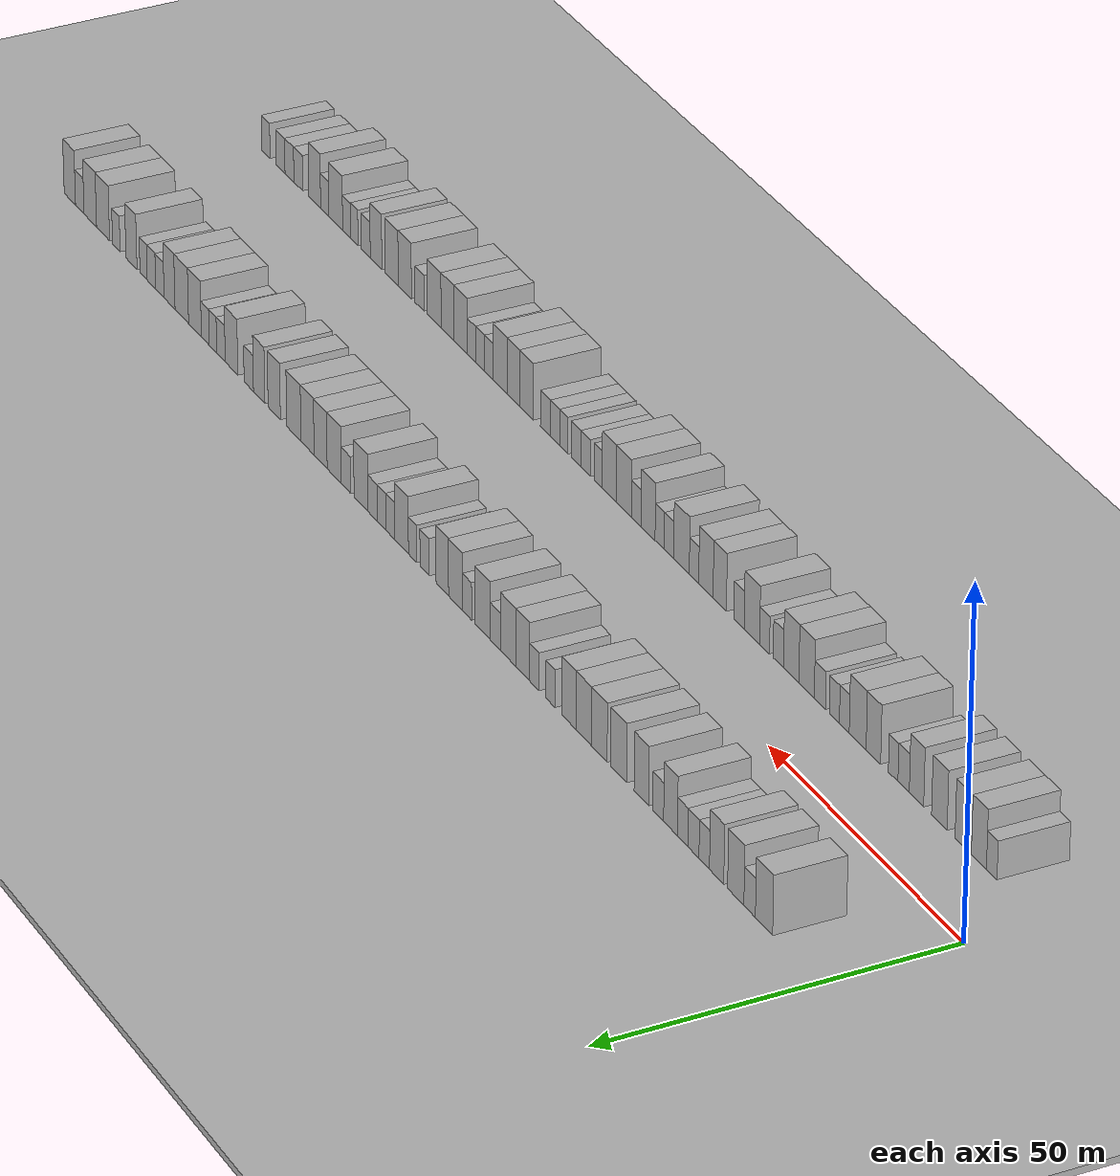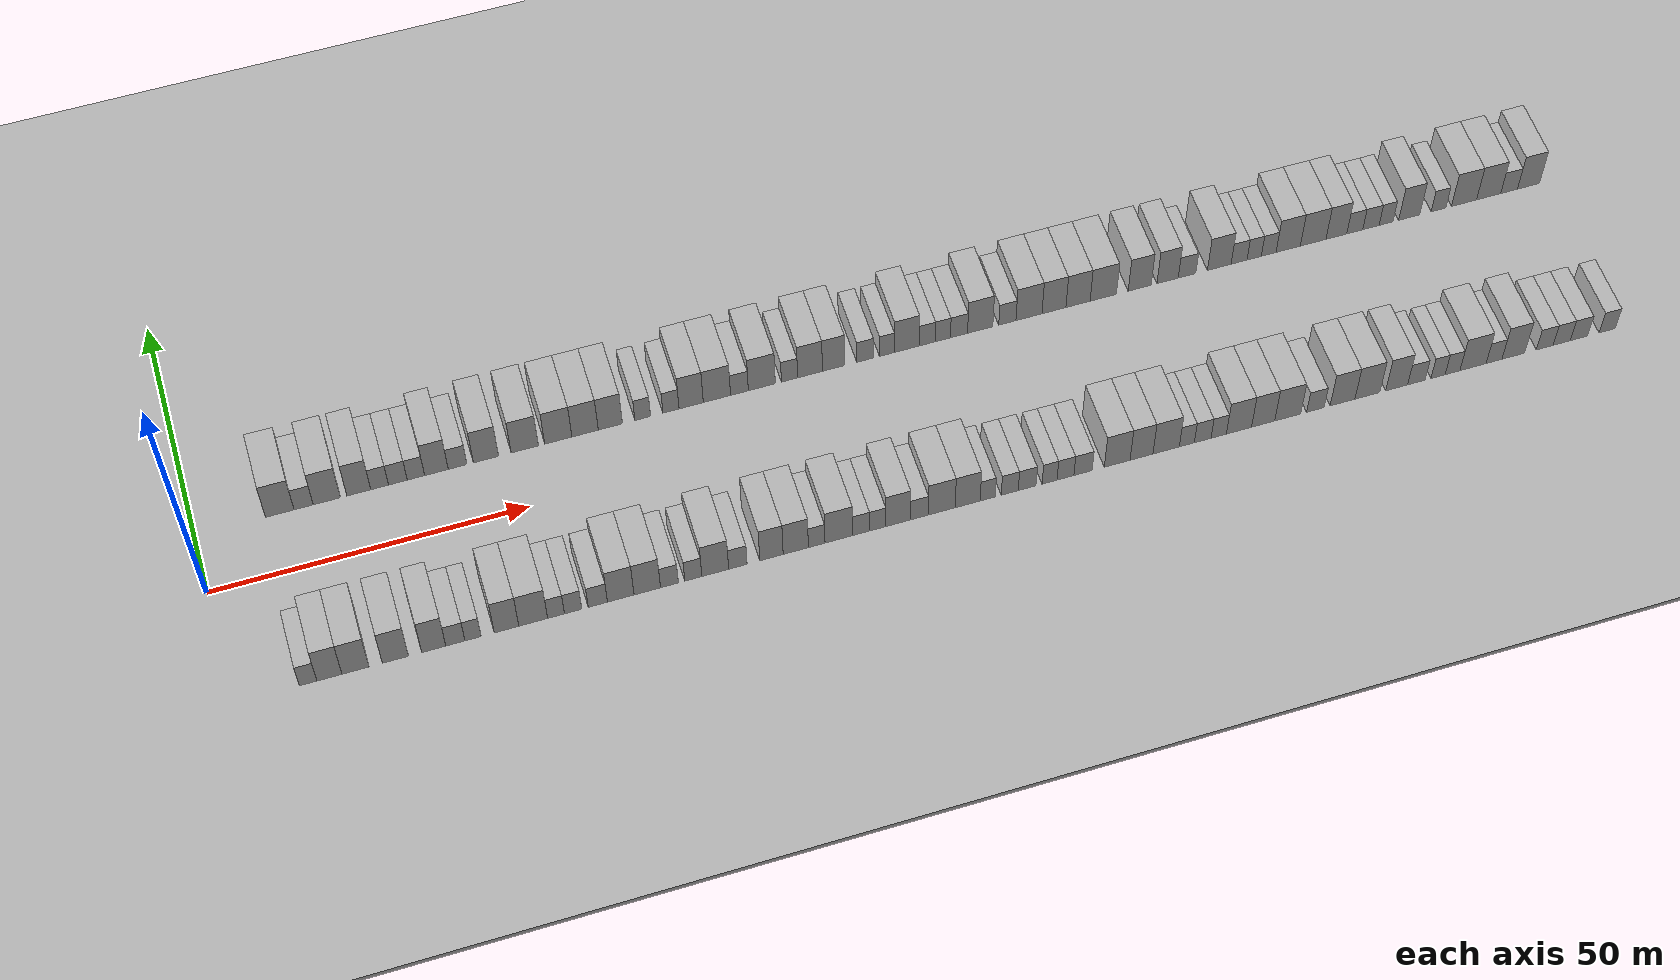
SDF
<?xml version="1.0" encoding="utf-8"?>

<sdf version="1.6">

   <world name="default">

      <gui fullscreen="0">

         <camera name="user_camera">

            <pose>-15 0 4.57585 0 0 0</pose>

            <view_controller>orbit</view_controller>

         </camera>

      </gui>

      <scene>

         <sky>

           <clouds>

             <speed>12</speed>

           </clouds>

         </sky>

         <ambient>0.4 0.4 0.4 1</ambient>

         <background>0.7 0.7 0.7 1</background>

         <shadows>1</shadows>

      </scene>

      <gravity>0 0 -9.8066</gravity>

      <magnetic_field>6e-06 2.3e-05 -4.2e-05</magnetic_field>

      <physics default="0" name="default_physics" type="ode">

         <ode>

            <solver>

               <type>quick</type>

               <iters>10</iters>

               <sor>1.0</sor>

               <use_dynamic_moi_rescaling>0</use_dynamic_moi_rescaling>

            </solver>

            <constraints>

               <cfm>0</cfm>

               <erp>0.2</erp>

               <contact_max_correcting_vel>100</contact_max_correcting_vel>

               <contact_surface_layer>0.001</contact_surface_layer>

            </constraints>

         </ode>

         <max_step_size>0.004</max_step_size>

         <real_time_factor>1</real_time_factor>

         <real_time_update_rate>250</real_time_update_rate>

      </physics>

      <light name="sun" type="directional">

         <cast_shadows>1</cast_shadows>

         <pose>0 0 10 0 0 0</pose>

         <diffuse>0.8 0.8 0.8 1</diffuse>

         <specular>0.2 0.2 0.2 1</specular>

         <attenuation>

            <range>1000</range>

            <constant>0.9</constant>

            <linear>0.01</linear>

            <quadratic>0.001</quadratic>

         </attenuation>

         <direction>-0.5 0.1 -0.9</direction>

      </light>

      <include>

         <name>ground_plane_1</name>

         <uri>model://HANNAS_ground_plane</uri>

         <pose>0 0 0  0 0 0</pose>

      </include>

      <include>

         <name>ground_plane_2</name>

         <uri>model://HANNAS_ground_plane</uri>

         <pose>100 0 0  0 0 0</pose>

      </include>

      <model name="building_1">

         <static>1</static>

         <pose frame="">13.2188 15.0000 0 0.000000 0.000000 1.570796</pose>

         <link name="link">

            <pose frame="">0 0 4.50 0 0 0</pose>

            <collision name="collision">

               <geometry>

                  <box>

                     <size>10.0000 4.4376 9.0000</size>

                  </box>

               </geometry>

               <max_contacts>10</max_contacts>

               <surface>

                  <contact>

                     <ode/>

                  </contact>

                  <bounce/>

                  <friction>

                     <torsional>

                        <ode/>

                     </torsional>

                     <ode/>

                  </friction>

               </surface>

            </collision>

            <visual name="visual">

               <cast_shadows>0</cast_shadows>

               <geometry>

                  <box>

                     <size>10.0000 4.4376 9.0000</size>

                  </box>

               </geometry>

               <material>

                  <script>

                     <uri>model://HANNAS_wall/materials/scripts</uri>

                     <uri>model://HANNAS_wall/materials/textures</uri>

                     <name>vrc/HANNAS_wall</name>

                  </script>

               </material>

            </visual>

            <self_collide>0</self_collide>

            <enable_wind>0</enable_wind>

            <kinematic>0</kinematic>

         </link>

      </model>

      <model name="building_2">

         <static>1</static>

         <pose frame="">16.9260 15.0000 0 0.000000 0.000000 1.570796</pose>

         <link name="link">

            <pose frame="">0 0 3.00 0 0 0</pose>

            <collision name="collision">

               <geometry>

                  <box>

                     <size>10.0000 2.9768 6.0000</size>

                  </box>

               </geometry>

               <max_contacts>10</max_contacts>

               <surface>

                  <contact>

                     <ode/>

                  </contact>

                  <bounce/>

                  <friction>

                     <torsional>

                        <ode/>

                     </torsional>

                     <ode/>

                  </friction>

               </surface>

            </collision>

            <visual name="visual">

               <cast_shadows>0</cast_shadows>

               <geometry>

                  <box>

                     <size>10.0000 2.9768 6.0000</size>

                  </box>

               </geometry>

               <material>

                  <script>

                     <uri>model://HANNAS_wall/materials/scripts</uri>

                     <uri>model://HANNAS_wall/materials/textures</uri>

                     <name>vrc/HANNAS_wall</name>

                  </script>

               </material>

            </visual>

            <self_collide>0</self_collide>

            <enable_wind>0</enable_wind>

            <kinematic>0</kinematic>

         </link>

      </model>

      <model name="building_3">

         <static>1</static>

         <pose frame="">20.5367 15.0000 0 0.000000 0.000000 1.570796</pose>

         <link name="link">

            <pose frame="">0 0 4.50 0 0 0</pose>

            <collision name="collision">

               <geometry>

                  <box>

                     <size>10.0000 4.2446 9.0000</size>

                  </box>

               </geometry>

               <max_contacts>10</max_contacts>

               <surface>

                  <contact>

                     <ode/>

                  </contact>

                  <bounce/>

                  <friction>

                     <torsional>

                        <ode/>

                     </torsional>

                     <ode/>

                  </friction>

               </surface>

            </collision>

            <visual name="visual">

               <cast_shadows>0</cast_shadows>

               <geometry>

                  <box>

                     <size>10.0000 4.2446 9.0000</size>

                  </box>

               </geometry>

               <material>

                  <script>

                     <uri>model://HANNAS_wall/materials/scripts</uri>

                     <uri>model://HANNAS_wall/materials/textures</uri>

                     <name>vrc/HANNAS_wall</name>

                  </script>

               </material>

            </visual>

            <self_collide>0</self_collide>

            <enable_wind>0</enable_wind>

            <kinematic>0</kinematic>

         </link>

      </model>

      <model name="building_4">

         <static>1</static>

         <pose frame="">25.5316 15.0000 0 0.000000 0.000000 1.570796</pose>

         <link name="link">

            <pose frame="">0 0 4.50 0 0 0</pose>

            <collision name="collision">

               <geometry>

                  <box>

                     <size>10.0000 3.7453 9.0000</size>

                  </box>

               </geometry>

               <max_contacts>10</max_contacts>

               <surface>

                  <contact>

                     <ode/>

                  </contact>

                  <bounce/>

                  <friction>

                     <torsional>

                        <ode/>

                     </torsional>

                     <ode/>

                  </friction>

               </surface>

            </collision>

            <visual name="visual">

               <cast_shadows>0</cast_shadows>

               <geometry>

                  <box>

                     <size>10.0000 3.7453 9.0000</size>

                  </box>

               </geometry>

               <material>

                  <script>

                     <uri>model://HANNAS_wall/materials/scripts</uri>

                     <uri>model://HANNAS_wall/materials/textures</uri>

                     <name>vrc/HANNAS_wall</name>

                  </script>

               </material>

            </visual>

            <self_collide>0</self_collide>

            <enable_wind>0</enable_wind>

            <kinematic>0</kinematic>

         </link>

      </model>

      <model name="building_5">

         <static>1</static>

         <pose frame="">28.7888 15.0000 0 0.000000 0.000000 1.570796</pose>

         <link name="link">

            <pose frame="">0 0 3.00 0 0 0</pose>

            <collision name="collision">

               <geometry>

                  <box>

                     <size>10.0000 2.7692 6.0000</size>

                  </box>

               </geometry>

               <max_contacts>10</max_contacts>

               <surface>

                  <contact>

                     <ode/>

                  </contact>

                  <bounce/>

                  <friction>

                     <torsional>

                        <ode/>

                     </torsional>

                     <ode/>

                  </friction>

               </surface>

            </collision>

            <visual name="visual">

               <cast_shadows>0</cast_shadows>

               <geometry>

                  <box>

                     <size>10.0000 2.7692 6.0000</size>

                  </box>

               </geometry>

               <material>

                  <script>

                     <uri>model://HANNAS_wall/materials/scripts</uri>

                     <uri>model://HANNAS_wall/materials/textures</uri>

                     <name>vrc/HANNAS_wall</name>

                  </script>

               </material>

            </visual>

            <self_collide>0</self_collide>

            <enable_wind>0</enable_wind>

            <kinematic>0</kinematic>

         </link>

      </model>

      <model name="building_6">

         <static>1</static>

         <pose frame="">31.6491 15.0000 0 0.000000 0.000000 1.570796</pose>

         <link name="link">

            <pose frame="">0 0 3.00 0 0 0</pose>

            <collision name="collision">

               <geometry>

                  <box>

                     <size>10.0000 2.9513 6.0000</size>

                  </box>

               </geometry>

               <max_contacts>10</max_contacts>

               <surface>

                  <contact>

                     <ode/>

                  </contact>

                  <bounce/>

                  <friction>

                     <torsional>

                        <ode/>

                     </torsional>

                     <ode/>

                  </friction>

               </surface>

            </collision>

            <visual name="visual">

               <cast_shadows>0</cast_shadows>

               <geometry>

                  <box>

                     <size>10.0000 2.9513 6.0000</size>

                  </box>

               </geometry>

               <material>

                  <script>

                     <uri>model://HANNAS_wall/materials/scripts</uri>

                     <uri>model://HANNAS_wall/materials/textures</uri>

                     <name>vrc/HANNAS_wall</name>

                  </script>

               </material>

            </visual>

            <self_collide>0</self_collide>

            <enable_wind>0</enable_wind>

            <kinematic>0</kinematic>

         </link>

      </model>

      <model name="building_7">

         <static>1</static>

         <pose frame="">34.4945 15.0000 0 0.000000 0.000000 1.570796</pose>

         <link name="link">

            <pose frame="">0 0 3.00 0 0 0</pose>

            <collision name="collision">

               <geometry>

                  <box>

                     <size>10.0000 2.7396 6.0000</size>

                  </box>

               </geometry>

               <max_contacts>10</max_contacts>

               <surface>

                  <contact>

                     <ode/>

                  </contact>

                  <bounce/>

                  <friction>

                     <torsional>

                        <ode/>

                     </torsional>

                     <ode/>

                  </friction>

               </surface>

            </collision>

            <visual name="visual">

               <cast_shadows>0</cast_shadows>

               <geometry>

                  <box>

                     <size>10.0000 2.7396 6.0000</size>

                  </box>

               </geometry>

               <material>

                  <script>

                     <uri>model://HANNAS_wall/materials/scripts</uri>

                     <uri>model://HANNAS_wall/materials/textures</uri>

                     <name>vrc/HANNAS_wall</name>

                  </script>

               </material>

            </visual>

            <self_collide>0</self_collide>

            <enable_wind>0</enable_wind>

            <kinematic>0</kinematic>

         </link>

      </model>

      <model name="building_8">

         <static>1</static>

         <pose frame="">37.7245 15.0000 0 0.000000 0.000000 1.570796</pose>

         <link name="link">

            <pose frame="">0 0 4.50 0 0 0</pose>

            <collision name="collision">

               <geometry>

                  <box>

                     <size>10.0000 3.7204 9.0000</size>

                  </box>

               </geometry>

               <max_contacts>10</max_contacts>

               <surface>

                  <contact>

                     <ode/>

                  </contact>

                  <bounce/>

                  <friction>

                     <torsional>

                        <ode/>

                     </torsional>

                     <ode/>

                  </friction>

               </surface>

            </collision>

            <visual name="visual">

               <cast_shadows>0</cast_shadows>

               <geometry>

                  <box>

                     <size>10.0000 3.7204 9.0000</size>

                  </box>

               </geometry>

               <material>

                  <script>

                     <uri>model://HANNAS_wall/materials/scripts</uri>

                     <uri>model://HANNAS_wall/materials/textures</uri>

                     <name>vrc/HANNAS_wall</name>

                  </script>

               </material>

            </visual>

            <self_collide>0</self_collide>

            <enable_wind>0</enable_wind>

            <kinematic>0</kinematic>

         </link>

      </model>

      <model name="building_9">

         <static>1</static>

         <pose frame="">41.0655 15.0000 0 0.000000 0.000000 1.570796</pose>

         <link name="link">

            <pose frame="">0 0 3.00 0 0 0</pose>

            <collision name="collision">

               <geometry>

                  <box>

                     <size>10.0000 2.9615 6.0000</size>

                  </box>

               </geometry>

               <max_contacts>10</max_contacts>

               <surface>

                  <contact>

                     <ode/>

                  </contact>

                  <bounce/>

                  <friction>

                     <torsional>

                        <ode/>

                     </torsional>

                     <ode/>

                  </friction>

               </surface>

            </collision>

            <visual name="visual">

               <cast_shadows>0</cast_shadows>

               <geometry>

                  <box>

                     <size>10.0000 2.9615 6.0000</size>

                  </box>

               </geometry>

               <material>

                  <script>

                     <uri>model://HANNAS_wall/materials/scripts</uri>

                     <uri>model://HANNAS_wall/materials/textures</uri>

                     <name>vrc/HANNAS_wall</name>

                  </script>

               </material>

            </visual>

            <self_collide>0</self_collide>

            <enable_wind>0</enable_wind>

            <kinematic>0</kinematic>

         </link>

      </model>

      <model name="building_10">

         <static>1</static>

         <pose frame="">45.5478 15.0000 0 0.000000 0.000000 1.570796</pose>

         <link name="link">

            <pose frame="">0 0 4.50 0 0 0</pose>

            <collision name="collision">

               <geometry>

                  <box>

                     <size>10.0000 4.0031 9.0000</size>

                  </box>

               </geometry>

               <max_contacts>10</max_contacts>

               <surface>

                  <contact>

                     <ode/>

                  </contact>

                  <bounce/>

                  <friction>

                     <torsional>

                        <ode/>

                     </torsional>

                     <ode/>

                  </friction>

               </surface>

            </collision>

            <visual name="visual">

               <cast_shadows>0</cast_shadows>

               <geometry>

                  <box>

                     <size>10.0000 4.0031 9.0000</size>

                  </box>

               </geometry>

               <material>

                  <script>

                     <uri>model://HANNAS_wall/materials/scripts</uri>

                     <uri>model://HANNAS_wall/materials/textures</uri>

                     <name>vrc/HANNAS_wall</name>

                  </script>

               </material>

            </visual>

            <self_collide>0</self_collide>

            <enable_wind>0</enable_wind>

            <kinematic>0</kinematic>

         </link>

      </model>

      <model name="building_11">

         <static>1</static>

         <pose frame="">51.7211 15.0000 0 0.000000 0.000000 1.570796</pose>

         <link name="link">

            <pose frame="">0 0 4.50 0 0 0</pose>

            <collision name="collision">

               <geometry>

                  <box>

                     <size>10.0000 4.3435 9.0000</size>

                  </box>

               </geometry>

               <max_contacts>10</max_contacts>

               <surface>

                  <contact>

                     <ode/>

                  </contact>

                  <bounce/>

                  <friction>

                     <torsional>

                        <ode/>

                     </torsional>

                     <ode/>

                  </friction>

               </surface>

            </collision>

            <visual name="visual">

               <cast_shadows>0</cast_shadows>

               <geometry>

                  <box>

                     <size>10.0000 4.3435 9.0000</size>

                  </box>

               </geometry>

               <material>

                  <script>

                     <uri>model://HANNAS_wall/materials/scripts</uri>

                     <uri>model://HANNAS_wall/materials/textures</uri>

                     <name>vrc/HANNAS_wall</name>

                  </script>

               </material>

            </visual>

            <self_collide>0</self_collide>

            <enable_wind>0</enable_wind>

            <kinematic>0</kinematic>

         </link>

      </model>

      <model name="building_12">

         <static>1</static>

         <pose frame="">57.0680 15.0000 0 0.000000 0.000000 1.570796</pose>

         <link name="link">

            <pose frame="">0 0 4.50 0 0 0</pose>

            <collision name="collision">

               <geometry>

                  <box>

                     <size>10.0000 4.3503 9.0000</size>

                  </box>

               </geometry>

               <max_contacts>10</max_contacts>

               <surface>

                  <contact>

                     <ode/>

                  </contact>

                  <bounce/>

                  <friction>

                     <torsional>

                        <ode/>

                     </torsional>

                     <ode/>

                  </friction>

               </surface>

            </collision>

            <visual name="visual">

               <cast_shadows>0</cast_shadows>

               <geometry>

                  <box>

                     <size>10.0000 4.3503 9.0000</size>

                  </box>

               </geometry>

               <material>

                  <script>

                     <uri>model://HANNAS_wall/materials/scripts</uri>

                     <uri>model://HANNAS_wall/materials/textures</uri>

                     <name>vrc/HANNAS_wall</name>

                  </script>

               </material>

            </visual>

            <self_collide>0</self_collide>

            <enable_wind>0</enable_wind>

            <kinematic>0</kinematic>

         </link>

      </model>

      <model name="building_13">

         <static>1</static>

         <pose frame="">61.3553 15.0000 0 0.000000 0.000000 1.570796</pose>

         <link name="link">

            <pose frame="">0 0 4.50 0 0 0</pose>

            <collision name="collision">

               <geometry>

                  <box>

                     <size>10.0000 4.2243 9.0000</size>

                  </box>

               </geometry>

               <max_contacts>10</max_contacts>

               <surface>

                  <contact>

                     <ode/>

                  </contact>

                  <bounce/>

                  <friction>

                     <torsional>

                        <ode/>

                     </torsional>

                     <ode/>

                  </friction>

               </surface>

            </collision>

            <visual name="visual">

               <cast_shadows>0</cast_shadows>

               <geometry>

                  <box>

                     <size>10.0000 4.2243 9.0000</size>

                  </box>

               </geometry>

               <material>

                  <script>

                     <uri>model://HANNAS_wall/materials/scripts</uri>

                     <uri>model://HANNAS_wall/materials/textures</uri>

                     <name>vrc/HANNAS_wall</name>

                  </script>

               </material>

            </visual>

            <self_collide>0</self_collide>

            <enable_wind>0</enable_wind>

            <kinematic>0</kinematic>

         </link>

      </model>

      <model name="building_14">

         <static>1</static>

         <pose frame="">65.4110 15.0000 0 0.000000 0.000000 1.570796</pose>

         <link name="link">

            <pose frame="">0 0 4.50 0 0 0</pose>

            <collision name="collision">

               <geometry>

                  <box>

                     <size>10.0000 3.8870 9.0000</size>

                  </box>

               </geometry>

               <max_contacts>10</max_contacts>

               <surface>

                  <contact>

                     <ode/>

                  </contact>

                  <bounce/>

                  <friction>

                     <torsional>

                        <ode/>

                     </torsional>

                     <ode/>

                  </friction>

               </surface>

            </collision>

            <visual name="visual">

               <cast_shadows>0</cast_shadows>

               <geometry>

                  <box>

                     <size>10.0000 3.8870 9.0000</size>

                  </box>

               </geometry>

               <material>

                  <script>

                     <uri>model://HANNAS_wall/materials/scripts</uri>

                     <uri>model://HANNAS_wall/materials/textures</uri>

                     <name>vrc/HANNAS_wall</name>

                  </script>

               </material>

            </visual>

            <self_collide>0</self_collide>

            <enable_wind>0</enable_wind>

            <kinematic>0</kinematic>

         </link>

      </model>

      <model name="building_15">

         <static>1</static>

         <pose frame="">70.6132 15.0000 0 0.000000 0.000000 1.570796</pose>

         <link name="link">

            <pose frame="">0 0 3.00 0 0 0</pose>

            <collision name="collision">

               <geometry>

                  <box>

                     <size>10.0000 2.5174 6.0000</size>

                  </box>

               </geometry>

               <max_contacts>10</max_contacts>

               <surface>

                  <contact>

                     <ode/>

                  </contact>

                  <bounce/>

                  <friction>

                     <torsional>

                        <ode/>

                     </torsional>

                     <ode/>

                  </friction>

               </surface>

            </collision>

            <visual name="visual">

               <cast_shadows>0</cast_shadows>

               <geometry>

                  <box>

                     <size>10.0000 2.5174 6.0000</size>

                  </box>

               </geometry>

               <material>

                  <script>

                     <uri>model://HANNAS_wall/materials/scripts</uri>

                     <uri>model://HANNAS_wall/materials/textures</uri>

                     <name>vrc/HANNAS_wall</name>

                  </script>

               </material>

            </visual>

            <self_collide>0</self_collide>

            <enable_wind>0</enable_wind>

            <kinematic>0</kinematic>

         </link>

      </model>

      <model name="building_16">

         <static>1</static>

         <pose frame="">75.1780 15.0000 0 0.000000 0.000000 1.570796</pose>

         <link name="link">

            <pose frame="">0 0 3.00 0 0 0</pose>

            <collision name="collision">

               <geometry>

                  <box>

                     <size>10.0000 2.6121 6.0000</size>

                  </box>

               </geometry>

               <max_contacts>10</max_contacts>

               <surface>

                  <contact>

                     <ode/>

                  </contact>

                  <bounce/>

                  <friction>

                     <torsional>

                        <ode/>

                     </torsional>

                     <ode/>

                  </friction>

               </surface>

            </collision>

            <visual name="visual">

               <cast_shadows>0</cast_shadows>

               <geometry>

                  <box>

                     <size>10.0000 2.6121 6.0000</size>

                  </box>

               </geometry>

               <material>

                  <script>

                     <uri>model://HANNAS_wall/materials/scripts</uri>

                     <uri>model://HANNAS_wall/materials/textures</uri>

                     <name>vrc/HANNAS_wall</name>

                  </script>

               </material>

            </visual>

            <self_collide>0</self_collide>

            <enable_wind>0</enable_wind>

            <kinematic>0</kinematic>

         </link>

      </model>

      <model name="building_17">

         <static>1</static>

         <pose frame="">78.4476 15.0000 0 0.000000 0.000000 1.570796</pose>

         <link name="link">

            <pose frame="">0 0 4.50 0 0 0</pose>

            <collision name="collision">

               <geometry>

                  <box>

                     <size>10.0000 3.9272 9.0000</size>

                  </box>

               </geometry>

               <max_contacts>10</max_contacts>

               <surface>

                  <contact>

                     <ode/>

                  </contact>

                  <bounce/>

                  <friction>

                     <torsional>

                        <ode/>

                     </torsional>

                     <ode/>

                  </friction>

               </surface>

            </collision>

            <visual name="visual">

               <cast_shadows>0</cast_shadows>

               <geometry>

                  <box>

                     <size>10.0000 3.9272 9.0000</size>

                  </box>

               </geometry>

               <material>

                  <script>

                     <uri>model://HANNAS_wall/materials/scripts</uri>

                     <uri>model://HANNAS_wall/materials/textures</uri>

                     <name>vrc/HANNAS_wall</name>

                  </script>

               </material>

            </visual>

            <self_collide>0</self_collide>

            <enable_wind>0</enable_wind>

            <kinematic>0</kinematic>

         </link>

      </model>

      <model name="building_18">

         <static>1</static>

         <pose frame="">82.6273 15.0000 0 0.000000 0.000000 1.570796</pose>

         <link name="link">

            <pose frame="">0 0 4.50 0 0 0</pose>

            <collision name="collision">

               <geometry>

                  <box>

                     <size>10.0000 4.4322 9.0000</size>

                  </box>

               </geometry>

               <max_contacts>10</max_contacts>

               <surface>

                  <contact>

                     <ode/>

                  </contact>

                  <bounce/>

                  <friction>

                     <torsional>

                        <ode/>

                     </torsional>

                     <ode/>

                  </friction>

               </surface>

            </collision>

            <visual name="visual">

               <cast_shadows>0</cast_shadows>

               <geometry>

                  <box>

                     <size>10.0000 4.4322 9.0000</size>

                  </box>

               </geometry>

               <material>

                  <script>

                     <uri>model://HANNAS_wall/materials/scripts</uri>

                     <uri>model://HANNAS_wall/materials/textures</uri>

                     <name>vrc/HANNAS_wall</name>

                  </script>

               </material>

            </visual>

            <self_collide>0</self_collide>

            <enable_wind>0</enable_wind>

            <kinematic>0</kinematic>

         </link>

      </model>

      <model name="building_19">

         <static>1</static>

         <pose frame="">86.2931 15.0000 0 0.000000 0.000000 1.570796</pose>

         <link name="link">

            <pose frame="">0 0 3.00 0 0 0</pose>

            <collision name="collision">

               <geometry>

                  <box>

                     <size>10.0000 2.8995 6.0000</size>

                  </box>

               </geometry>

               <max_contacts>10</max_contacts>

               <surface>

                  <contact>

                     <ode/>

                  </contact>

                  <bounce/>

                  <friction>

                     <torsional>

                        <ode/>

                     </torsional>

                     <ode/>

                  </friction>

               </surface>

            </collision>

            <visual name="visual">

               <cast_shadows>0</cast_shadows>

               <geometry>

                  <box>

                     <size>10.0000 2.8995 6.0000</size>

                  </box>

               </geometry>

               <material>

                  <script>

                     <uri>model://HANNAS_wall/materials/scripts</uri>

                     <uri>model://HANNAS_wall/materials/textures</uri>

                     <name>vrc/HANNAS_wall</name>

                  </script>

               </material>

            </visual>

            <self_collide>0</self_collide>

            <enable_wind>0</enable_wind>

            <kinematic>0</kinematic>

         </link>

      </model>

      <model name="building_20">

         <static>1</static>

         <pose frame="">89.9431 15.0000 0 0.000000 0.000000 1.570796</pose>

         <link name="link">

            <pose frame="">0 0 4.50 0 0 0</pose>

            <collision name="collision">

               <geometry>

                  <box>

                     <size>10.0000 4.4005 9.0000</size>

                  </box>

               </geometry>

               <max_contacts>10</max_contacts>

               <surface>

                  <contact>

                     <ode/>

                  </contact>

                  <bounce/>

                  <friction>

                     <torsional>

                        <ode/>

                     </torsional>

                     <ode/>

                  </friction>

               </surface>

            </collision>

            <visual name="visual">

               <cast_shadows>0</cast_shadows>

               <geometry>

                  <box>

                     <size>10.0000 4.4005 9.0000</size>

                  </box>

               </geometry>

               <material>

                  <script>

                     <uri>model://HANNAS_wall/materials/scripts</uri>

                     <uri>model://HANNAS_wall/materials/textures</uri>

                     <name>vrc/HANNAS_wall</name>

                  </script>

               </material>

            </visual>

            <self_collide>0</self_collide>

            <enable_wind>0</enable_wind>

            <kinematic>0</kinematic>

         </link>

      </model>

      <model name="building_21">

         <static>1</static>

         <pose frame="">94.4690 15.0000 0 0.000000 0.000000 1.570796</pose>

         <link name="link">

            <pose frame="">0 0 3.00 0 0 0</pose>

            <collision name="collision">

               <geometry>

                  <box>

                     <size>10.0000 2.6513 6.0000</size>

                  </box>

               </geometry>

               <max_contacts>10</max_contacts>

               <surface>

                  <contact>

                     <ode/>

                  </contact>

                  <bounce/>

                  <friction>

                     <torsional>

                        <ode/>

                     </torsional>

                     <ode/>

                  </friction>

               </surface>

            </collision>

            <visual name="visual">

               <cast_shadows>0</cast_shadows>

               <geometry>

                  <box>

                     <size>10.0000 2.6513 6.0000</size>

                  </box>

               </geometry>

               <material>

                  <script>

                     <uri>model://HANNAS_wall/materials/scripts</uri>

                     <uri>model://HANNAS_wall/materials/textures</uri>

                     <name>vrc/HANNAS_wall</name>

                  </script>

               </material>

            </visual>

            <self_collide>0</self_collide>

            <enable_wind>0</enable_wind>

            <kinematic>0</kinematic>

         </link>

      </model>

      <model name="building_22">

         <static>1</static>

         <pose frame="">97.8308 15.0000 0 0.000000 0.000000 1.570796</pose>

         <link name="link">

            <pose frame="">0 0 4.50 0 0 0</pose>

            <collision name="collision">

               <geometry>

                  <box>

                     <size>10.0000 4.0723 9.0000</size>

                  </box>

               </geometry>

               <max_contacts>10</max_contacts>

               <surface>

                  <contact>

                     <ode/>

                  </contact>

                  <bounce/>

                  <friction>

                     <torsional>

                        <ode/>

                     </torsional>

                     <ode/>

                  </friction>

               </surface>

            </collision>

            <visual name="visual">

               <cast_shadows>0</cast_shadows>

               <geometry>

                  <box>

                     <size>10.0000 4.0723 9.0000</size>

                  </box>

               </geometry>

               <material>

                  <script>

                     <uri>model://HANNAS_wall/materials/scripts</uri>

                     <uri>model://HANNAS_wall/materials/textures</uri>

                     <name>vrc/HANNAS_wall</name>

                  </script>

               </material>

            </visual>

            <self_collide>0</self_collide>

            <enable_wind>0</enable_wind>

            <kinematic>0</kinematic>

         </link>

      </model>

      <model name="building_23">

         <static>1</static>

         <pose frame="">101.7011 15.0000 0 0.000000 0.000000 1.570796</pose>

         <link name="link">

            <pose frame="">0 0 4.50 0 0 0</pose>

            <collision name="collision">

               <geometry>

                  <box>

                     <size>10.0000 3.6684 9.0000</size>

                  </box>

               </geometry>

               <max_contacts>10</max_contacts>

               <surface>

                  <contact>

                     <ode/>

                  </contact>

                  <bounce/>

                  <friction>

                     <torsional>

                        <ode/>

                     </torsional>

                     <ode/>

                  </friction>

               </surface>

            </collision>

            <visual name="visual">

               <cast_shadows>0</cast_shadows>

               <geometry>

                  <box>

                     <size>10.0000 3.6684 9.0000</size>

                  </box>

               </geometry>

               <material>

                  <script>

                     <uri>model://HANNAS_wall/materials/scripts</uri>

                     <uri>model://HANNAS_wall/materials/textures</uri>

                     <name>vrc/HANNAS_wall</name>

                  </script>

               </material>

            </visual>

            <self_collide>0</self_collide>

            <enable_wind>0</enable_wind>

            <kinematic>0</kinematic>

         </link>

      </model>

      <model name="building_24">

         <static>1</static>

         <pose frame="">106.9101 15.0000 0 0.000000 0.000000 1.570796</pose>

         <link name="link">

            <pose frame="">0 0 3.00 0 0 0</pose>

            <collision name="collision">

               <geometry>

                  <box>

                     <size>10.0000 2.7494 6.0000</size>

                  </box>

               </geometry>

               <max_contacts>10</max_contacts>

               <surface>

                  <contact>

                     <ode/>

                  </contact>

                  <bounce/>

                  <friction>

                     <torsional>

                        <ode/>

                     </torsional>

                     <ode/>

                  </friction>

               </surface>

            </collision>

            <visual name="visual">

               <cast_shadows>0</cast_shadows>

               <geometry>

                  <box>

                     <size>10.0000 2.7494 6.0000</size>

                  </box>

               </geometry>

               <material>

                  <script>

                     <uri>model://HANNAS_wall/materials/scripts</uri>

                     <uri>model://HANNAS_wall/materials/textures</uri>

                     <name>vrc/HANNAS_wall</name>

                  </script>

               </material>

            </visual>

            <self_collide>0</self_collide>

            <enable_wind>0</enable_wind>

            <kinematic>0</kinematic>

         </link>

      </model>

      <model name="building_25">

         <static>1</static>

         <pose frame="">110.5071 15.0000 0 0.000000 0.000000 1.570796</pose>

         <link name="link">

            <pose frame="">0 0 3.00 0 0 0</pose>

            <collision name="collision">

               <geometry>

                  <box>

                     <size>10.0000 2.4445 6.0000</size>

                  </box>

               </geometry>

               <max_contacts>10</max_contacts>

               <surface>

                  <contact>

                     <ode/>

                  </contact>

                  <bounce/>

                  <friction>

                     <torsional>

                        <ode/>

                     </torsional>

                     <ode/>

                  </friction>

               </surface>

            </collision>

            <visual name="visual">

               <cast_shadows>0</cast_shadows>

               <geometry>

                  <box>

                     <size>10.0000 2.4445 6.0000</size>

                  </box>

               </geometry>

               <material>

                  <script>

                     <uri>model://HANNAS_wall/materials/scripts</uri>

                     <uri>model://HANNAS_wall/materials/textures</uri>

                     <name>vrc/HANNAS_wall</name>

                  </script>

               </material>

            </visual>

            <self_collide>0</self_collide>

            <enable_wind>0</enable_wind>

            <kinematic>0</kinematic>

         </link>

      </model>

      <model name="building_26">

         <static>1</static>

         <pose frame="">113.7879 15.0000 0 0.000000 0.000000 1.570796</pose>

         <link name="link">

            <pose frame="">0 0 4.50 0 0 0</pose>

            <collision name="collision">

               <geometry>

                  <box>

                     <size>10.0000 4.1172 9.0000</size>

                  </box>

               </geometry>

               <max_contacts>10</max_contacts>

               <surface>

                  <contact>

                     <ode/>

                  </contact>

                  <bounce/>

                  <friction>

                     <torsional>

                        <ode/>

                     </torsional>

                     <ode/>

                  </friction>

               </surface>

            </collision>

            <visual name="visual">

               <cast_shadows>0</cast_shadows>

               <geometry>

                  <box>

                     <size>10.0000 4.1172 9.0000</size>

                  </box>

               </geometry>

               <material>

                  <script>

                     <uri>model://HANNAS_wall/materials/scripts</uri>

                     <uri>model://HANNAS_wall/materials/textures</uri>

                     <name>vrc/HANNAS_wall</name>

                  </script>

               </material>

            </visual>

            <self_collide>0</self_collide>

            <enable_wind>0</enable_wind>

            <kinematic>0</kinematic>

         </link>

      </model>

      <model name="building_27">

         <static>1</static>

         <pose frame="">117.1877 15.0000 0 0.000000 0.000000 1.570796</pose>

         <link name="link">

            <pose frame="">0 0 3.00 0 0 0</pose>

            <collision name="collision">

               <geometry>

                  <box>

                     <size>10.0000 2.6824 6.0000</size>

                  </box>

               </geometry>

               <max_contacts>10</max_contacts>

               <surface>

                  <contact>

                     <ode/>

                  </contact>

                  <bounce/>

                  <friction>

                     <torsional>

                        <ode/>

                     </torsional>

                     <ode/>

                  </friction>

               </surface>

            </collision>

            <visual name="visual">

               <cast_shadows>0</cast_shadows>

               <geometry>

                  <box>

                     <size>10.0000 2.6824 6.0000</size>

                  </box>

               </geometry>

               <material>

                  <script>

                     <uri>model://HANNAS_wall/materials/scripts</uri>

                     <uri>model://HANNAS_wall/materials/textures</uri>

                     <name>vrc/HANNAS_wall</name>

                  </script>

               </material>

            </visual>

            <self_collide>0</self_collide>

            <enable_wind>0</enable_wind>

            <kinematic>0</kinematic>

         </link>

      </model>

      <model name="building_28">

         <static>1</static>

         <pose frame="">119.7982 15.0000 0 0.000000 0.000000 1.570796</pose>

         <link name="link">

            <pose frame="">0 0 3.00 0 0 0</pose>

            <collision name="collision">

               <geometry>

                  <box>

                     <size>10.0000 2.5385 6.0000</size>

                  </box>

               </geometry>

               <max_contacts>10</max_contacts>

               <surface>

                  <contact>

                     <ode/>

                  </contact>

                  <bounce/>

                  <friction>

                     <torsional>

                        <ode/>

                     </torsional>

                     <ode/>

                  </friction>

               </surface>

            </collision>

            <visual name="visual">

               <cast_shadows>0</cast_shadows>

               <geometry>

                  <box>

                     <size>10.0000 2.5385 6.0000</size>

                  </box>

               </geometry>

               <material>

                  <script>

                     <uri>model://HANNAS_wall/materials/scripts</uri>

                     <uri>model://HANNAS_wall/materials/textures</uri>

                     <name>vrc/HANNAS_wall</name>

                  </script>

               </material>

            </visual>

            <self_collide>0</self_collide>

            <enable_wind>0</enable_wind>

            <kinematic>0</kinematic>

         </link>

      </model>

      <model name="building_29">

         <static>1</static>

         <pose frame="">122.4933 15.0000 0 0.000000 0.000000 1.570796</pose>

         <link name="link">

            <pose frame="">0 0 3.00 0 0 0</pose>

            <collision name="collision">

               <geometry>

                  <box>

                     <size>10.0000 2.8517 6.0000</size>

                  </box>

               </geometry>

               <max_contacts>10</max_contacts>

               <surface>

                  <contact>

                     <ode/>

                  </contact>

                  <bounce/>

                  <friction>

                     <torsional>

                        <ode/>

                     </torsional>

                     <ode/>

                  </friction>

               </surface>

            </collision>

            <visual name="visual">

               <cast_shadows>0</cast_shadows>

               <geometry>

                  <box>

                     <size>10.0000 2.8517 6.0000</size>

                  </box>

               </geometry>

               <material>

                  <script>

                     <uri>model://HANNAS_wall/materials/scripts</uri>

                     <uri>model://HANNAS_wall/materials/textures</uri>

                     <name>vrc/HANNAS_wall</name>

                  </script>

               </material>

            </visual>

            <self_collide>0</self_collide>

            <enable_wind>0</enable_wind>

            <kinematic>0</kinematic>

         </link>

      </model>

      <model name="building_30">

         <static>1</static>

         <pose frame="">126.0310 15.0000 0 0.000000 0.000000 1.570796</pose>

         <link name="link">

            <pose frame="">0 0 4.50 0 0 0</pose>

            <collision name="collision">

               <geometry>

                  <box>

                     <size>10.0000 4.2237 9.0000</size>

                  </box>

               </geometry>

               <max_contacts>10</max_contacts>

               <surface>

                  <contact>

                     <ode/>

                  </contact>

                  <bounce/>

                  <friction>

                     <torsional>

                        <ode/>

                     </torsional>

                     <ode/>

                  </friction>

               </surface>

            </collision>

            <visual name="visual">

               <cast_shadows>0</cast_shadows>

               <geometry>

                  <box>

                     <size>10.0000 4.2237 9.0000</size>

                  </box>

               </geometry>

               <material>

                  <script>

                     <uri>model://HANNAS_wall/materials/scripts</uri>

                     <uri>model://HANNAS_wall/materials/textures</uri>

                     <name>vrc/HANNAS_wall</name>

                  </script>

               </material>

            </visual>

            <self_collide>0</self_collide>

            <enable_wind>0</enable_wind>

            <kinematic>0</kinematic>

         </link>

      </model>

      <model name="building_31">

         <static>1</static>

         <pose frame="">130.5884 15.0000 0 0.000000 0.000000 1.570796</pose>

         <link name="link">

            <pose frame="">0 0 3.00 0 0 0</pose>

            <collision name="collision">

               <geometry>

                  <box>

                     <size>10.0000 2.8909 6.0000</size>

                  </box>

               </geometry>

               <max_contacts>10</max_contacts>

               <surface>

                  <contact>

                     <ode/>

                  </contact>

                  <bounce/>

                  <friction>

                     <torsional>

                        <ode/>

                     </torsional>

                     <ode/>

                  </friction>

               </surface>

            </collision>

            <visual name="visual">

               <cast_shadows>0</cast_shadows>

               <geometry>

                  <box>

                     <size>10.0000 2.8909 6.0000</size>

                  </box>

               </geometry>

               <material>

                  <script>

                     <uri>model://HANNAS_wall/materials/scripts</uri>

                     <uri>model://HANNAS_wall/materials/textures</uri>

                     <name>vrc/HANNAS_wall</name>

                  </script>

               </material>

            </visual>

            <self_collide>0</self_collide>

            <enable_wind>0</enable_wind>

            <kinematic>0</kinematic>

         </link>

      </model>

      <model name="building_32">

         <static>1</static>

         <pose frame="">134.2233 15.0000 0 0.000000 0.000000 1.570796</pose>

         <link name="link">

            <pose frame="">0 0 4.50 0 0 0</pose>

            <collision name="collision">

               <geometry>

                  <box>

                     <size>10.0000 4.3790 9.0000</size>

                  </box>

               </geometry>

               <max_contacts>10</max_contacts>

               <surface>

                  <contact>

                     <ode/>

                  </contact>

                  <bounce/>

                  <friction>

                     <torsional>

                        <ode/>

                     </torsional>

                     <ode/>

                  </friction>

               </surface>

            </collision>

            <visual name="visual">

               <cast_shadows>0</cast_shadows>

               <geometry>

                  <box>

                     <size>10.0000 4.3790 9.0000</size>

                  </box>

               </geometry>

               <material>

                  <script>

                     <uri>model://HANNAS_wall/materials/scripts</uri>

                     <uri>model://HANNAS_wall/materials/textures</uri>

                     <name>vrc/HANNAS_wall</name>

                  </script>

               </material>

            </visual>

            <self_collide>0</self_collide>

            <enable_wind>0</enable_wind>

            <kinematic>0</kinematic>

         </link>

      </model>

      <model name="building_33">

         <static>1</static>

         <pose frame="">138.4308 15.0000 0 0.000000 0.000000 1.570796</pose>

         <link name="link">

            <pose frame="">0 0 4.50 0 0 0</pose>

            <collision name="collision">

               <geometry>

                  <box>

                     <size>10.0000 4.0360 9.0000</size>

                  </box>

               </geometry>

               <max_contacts>10</max_contacts>

               <surface>

                  <contact>

                     <ode/>

                  </contact>

                  <bounce/>

                  <friction>

                     <torsional>

                        <ode/>

                     </torsional>

                     <ode/>

                  </friction>

               </surface>

            </collision>

            <visual name="visual">

               <cast_shadows>0</cast_shadows>

               <geometry>

                  <box>

                     <size>10.0000 4.0360 9.0000</size>

                  </box>

               </geometry>

               <material>

                  <script>

                     <uri>model://HANNAS_wall/materials/scripts</uri>

                     <uri>model://HANNAS_wall/materials/textures</uri>

                     <name>vrc/HANNAS_wall</name>

                  </script>

               </material>

            </visual>

            <self_collide>0</self_collide>

            <enable_wind>0</enable_wind>

            <kinematic>0</kinematic>

         </link>

      </model>

      <model name="building_34">

         <static>1</static>

         <pose frame="">142.4952 15.0000 0 0.000000 0.000000 1.570796</pose>

         <link name="link">

            <pose frame="">0 0 4.50 0 0 0</pose>

            <collision name="collision">

               <geometry>

                  <box>

                     <size>10.0000 4.0927 9.0000</size>

                  </box>

               </geometry>

               <max_contacts>10</max_contacts>

               <surface>

                  <contact>

                     <ode/>

                  </contact>

                  <bounce/>

                  <friction>

                     <torsional>

                        <ode/>

                     </torsional>

                     <ode/>

                  </friction>

               </surface>

            </collision>

            <visual name="visual">

               <cast_shadows>0</cast_shadows>

               <geometry>

                  <box>

                     <size>10.0000 4.0927 9.0000</size>

                  </box>

               </geometry>

               <material>

                  <script>

                     <uri>model://HANNAS_wall/materials/scripts</uri>

                     <uri>model://HANNAS_wall/materials/textures</uri>

                     <name>vrc/HANNAS_wall</name>

                  </script>

               </material>

            </visual>

            <self_collide>0</self_collide>

            <enable_wind>0</enable_wind>

            <kinematic>0</kinematic>

         </link>

      </model>

      <model name="building_35">

         <static>1</static>

         <pose frame="">146.7730 15.0000 0 0.000000 0.000000 1.570796</pose>

         <link name="link">

            <pose frame="">0 0 4.50 0 0 0</pose>

            <collision name="collision">

               <geometry>

                  <box>

                     <size>10.0000 4.4629 9.0000</size>

                  </box>

               </geometry>

               <max_contacts>10</max_contacts>

               <surface>

                  <contact>

                     <ode/>

                  </contact>

                  <bounce/>

                  <friction>

                     <torsional>

                        <ode/>

                     </torsional>

                     <ode/>

                  </friction>

               </surface>

            </collision>

            <visual name="visual">

               <cast_shadows>0</cast_shadows>

               <geometry>

                  <box>

                     <size>10.0000 4.4629 9.0000</size>

                  </box>

               </geometry>

               <material>

                  <script>

                     <uri>model://HANNAS_wall/materials/scripts</uri>

                     <uri>model://HANNAS_wall/materials/textures</uri>

                     <name>vrc/HANNAS_wall</name>

                  </script>

               </material>

            </visual>

            <self_collide>0</self_collide>

            <enable_wind>0</enable_wind>

            <kinematic>0</kinematic>

         </link>

      </model>

      <model name="building_36">

         <static>1</static>

         <pose frame="">152.9612 15.0000 0 0.000000 0.000000 1.570796</pose>

         <link name="link">

            <pose frame="">0 0 4.50 0 0 0</pose>

            <collision name="collision">

               <geometry>

                  <box>

                     <size>10.0000 3.9135 9.0000</size>

                  </box>

               </geometry>

               <max_contacts>10</max_contacts>

               <surface>

                  <contact>

                     <ode/>

                  </contact>

                  <bounce/>

                  <friction>

                     <torsional>

                        <ode/>

                     </torsional>

                     <ode/>

                  </friction>

               </surface>

            </collision>

            <visual name="visual">

               <cast_shadows>0</cast_shadows>

               <geometry>

                  <box>

                     <size>10.0000 3.9135 9.0000</size>

                  </box>

               </geometry>

               <material>

                  <script>

                     <uri>model://HANNAS_wall/materials/scripts</uri>

                     <uri>model://HANNAS_wall/materials/textures</uri>

                     <name>vrc/HANNAS_wall</name>

                  </script>

               </material>

            </visual>

            <self_collide>0</self_collide>

            <enable_wind>0</enable_wind>

            <kinematic>0</kinematic>

         </link>

      </model>

      <model name="building_37">

         <static>1</static>

         <pose frame="">157.7371 15.0000 0 0.000000 0.000000 1.570796</pose>

         <link name="link">

            <pose frame="">0 0 4.50 0 0 0</pose>

            <collision name="collision">

               <geometry>

                  <box>

                     <size>10.0000 3.6383 9.0000</size>

                  </box>

               </geometry>

               <max_contacts>10</max_contacts>

               <surface>

                  <contact>

                     <ode/>

                  </contact>

                  <bounce/>

                  <friction>

                     <torsional>

                        <ode/>

                     </torsional>

                     <ode/>

                  </friction>

               </surface>

            </collision>

            <visual name="visual">

               <cast_shadows>0</cast_shadows>

               <geometry>

                  <box>

                     <size>10.0000 3.6383 9.0000</size>

                  </box>

               </geometry>

               <material>

                  <script>

                     <uri>model://HANNAS_wall/materials/scripts</uri>

                     <uri>model://HANNAS_wall/materials/textures</uri>

                     <name>vrc/HANNAS_wall</name>

                  </script>

               </material>

            </visual>

            <self_collide>0</self_collide>

            <enable_wind>0</enable_wind>

            <kinematic>0</kinematic>

         </link>

      </model>

      <model name="building_38">

         <static>1</static>

         <pose frame="">161.0521 15.0000 0 0.000000 0.000000 1.570796</pose>

         <link name="link">

            <pose frame="">0 0 3.00 0 0 0</pose>

            <collision name="collision">

               <geometry>

                  <box>

                     <size>10.0000 2.9917 6.0000</size>

                  </box>

               </geometry>

               <max_contacts>10</max_contacts>

               <surface>

                  <contact>

                     <ode/>

                  </contact>

                  <bounce/>

                  <friction>

                     <torsional>

                        <ode/>

                     </torsional>

                     <ode/>

                  </friction>

               </surface>

            </collision>

            <visual name="visual">

               <cast_shadows>0</cast_shadows>

               <geometry>

                  <box>

                     <size>10.0000 2.9917 6.0000</size>

                  </box>

               </geometry>

               <material>

                  <script>

                     <uri>model://HANNAS_wall/materials/scripts</uri>

                     <uri>model://HANNAS_wall/materials/textures</uri>

                     <name>vrc/HANNAS_wall</name>

                  </script>

               </material>

            </visual>

            <self_collide>0</self_collide>

            <enable_wind>0</enable_wind>

            <kinematic>0</kinematic>

         </link>

      </model>

      <model name="building_39">

         <static>1</static>

         <pose frame="">166.5863 15.0000 0 0.000000 0.000000 1.570796</pose>

         <link name="link">

            <pose frame="">0 0 4.50 0 0 0</pose>

            <collision name="collision">

               <geometry>

                  <box>

                     <size>10.0000 4.0768 9.0000</size>

                  </box>

               </geometry>

               <max_contacts>10</max_contacts>

               <surface>

                  <contact>

                     <ode/>

                  </contact>

                  <bounce/>

                  <friction>

                     <torsional>

                        <ode/>

                     </torsional>

                     <ode/>

                  </friction>

               </surface>

            </collision>

            <visual name="visual">

               <cast_shadows>0</cast_shadows>

               <geometry>

                  <box>

                     <size>10.0000 4.0768 9.0000</size>

                  </box>

               </geometry>

               <material>

                  <script>

                     <uri>model://HANNAS_wall/materials/scripts</uri>

                     <uri>model://HANNAS_wall/materials/textures</uri>

                     <name>vrc/HANNAS_wall</name>

                  </script>

               </material>

            </visual>

            <self_collide>0</self_collide>

            <enable_wind>0</enable_wind>

            <kinematic>0</kinematic>

         </link>

      </model>

      <model name="building_40">

         <static>1</static>

         <pose frame="">169.9971 15.0000 0 0.000000 0.000000 1.570796</pose>

         <link name="link">

            <pose frame="">0 0 3.00 0 0 0</pose>

            <collision name="collision">

               <geometry>

                  <box>

                     <size>10.0000 2.7448 6.0000</size>

                  </box>

               </geometry>

               <max_contacts>10</max_contacts>

               <surface>

                  <contact>

                     <ode/>

                  </contact>

                  <bounce/>

                  <friction>

                     <torsional>

                        <ode/>

                     </torsional>

                     <ode/>

                  </friction>

               </surface>

            </collision>

            <visual name="visual">

               <cast_shadows>0</cast_shadows>

               <geometry>

                  <box>

                     <size>10.0000 2.7448 6.0000</size>

                  </box>

               </geometry>

               <material>

                  <script>

                     <uri>model://HANNAS_wall/materials/scripts</uri>

                     <uri>model://HANNAS_wall/materials/textures</uri>

                     <name>vrc/HANNAS_wall</name>

                  </script>

               </material>

            </visual>

            <self_collide>0</self_collide>

            <enable_wind>0</enable_wind>

            <kinematic>0</kinematic>

         </link>

      </model>

      <model name="building_41">

         <static>1</static>

         <pose frame="">172.5984 15.0000 0 0.000000 0.000000 1.570796</pose>

         <link name="link">

            <pose frame="">0 0 3.00 0 0 0</pose>

            <collision name="collision">

               <geometry>

                  <box>

                     <size>10.0000 2.4578 6.0000</size>

                  </box>

               </geometry>

               <max_contacts>10</max_contacts>

               <surface>

                  <contact>

                     <ode/>

                  </contact>

                  <bounce/>

                  <friction>

                     <torsional>

                        <ode/>

                     </torsional>

                     <ode/>

                  </friction>

               </surface>

            </collision>

            <visual name="visual">

               <cast_shadows>0</cast_shadows>

               <geometry>

                  <box>

                     <size>10.0000 2.4578 6.0000</size>

                  </box>

               </geometry>

               <material>

                  <script>

                     <uri>model://HANNAS_wall/materials/scripts</uri>

                     <uri>model://HANNAS_wall/materials/textures</uri>

                     <name>vrc/HANNAS_wall</name>

                  </script>

               </material>

            </visual>

            <self_collide>0</self_collide>

            <enable_wind>0</enable_wind>

            <kinematic>0</kinematic>

         </link>

      </model>

      <model name="building_42">

         <static>1</static>

         <pose frame="">175.1026 15.0000 0 0.000000 0.000000 1.570796</pose>

         <link name="link">

            <pose frame="">0 0 3.00 0 0 0</pose>

            <collision name="collision">

               <geometry>

                  <box>

                     <size>10.0000 2.5506 6.0000</size>

                  </box>

               </geometry>

               <max_contacts>10</max_contacts>

               <surface>

                  <contact>

                     <ode/>

                  </contact>

                  <bounce/>

                  <friction>

                     <torsional>

                        <ode/>

                     </torsional>

                     <ode/>

                  </friction>

               </surface>

            </collision>

            <visual name="visual">

               <cast_shadows>0</cast_shadows>

               <geometry>

                  <box>

                     <size>10.0000 2.5506 6.0000</size>

                  </box>

               </geometry>

               <material>

                  <script>

                     <uri>model://HANNAS_wall/materials/scripts</uri>

                     <uri>model://HANNAS_wall/materials/textures</uri>

                     <name>vrc/HANNAS_wall</name>

                  </script>

               </material>

            </visual>

            <self_collide>0</self_collide>

            <enable_wind>0</enable_wind>

            <kinematic>0</kinematic>

         </link>

      </model>

      <model name="building_43">

         <static>1</static>

         <pose frame="">178.4787 15.0000 0 0.000000 0.000000 1.570796</pose>

         <link name="link">

            <pose frame="">0 0 4.50 0 0 0</pose>

            <collision name="collision">

               <geometry>

                  <box>

                     <size>10.0000 4.2018 9.0000</size>

                  </box>

               </geometry>

               <max_contacts>10</max_contacts>

               <surface>

                  <contact>

                     <ode/>

                  </contact>

                  <bounce/>

                  <friction>

                     <torsional>

                        <ode/>

                     </torsional>

                     <ode/>

                  </friction>

               </surface>

            </collision>

            <visual name="visual">

               <cast_shadows>0</cast_shadows>

               <geometry>

                  <box>

                     <size>10.0000 4.2018 9.0000</size>

                  </box>

               </geometry>

               <material>

                  <script>

                     <uri>model://HANNAS_wall/materials/scripts</uri>

                     <uri>model://HANNAS_wall/materials/textures</uri>

                     <name>vrc/HANNAS_wall</name>

                  </script>

               </material>

            </visual>

            <self_collide>0</self_collide>

            <enable_wind>0</enable_wind>

            <kinematic>0</kinematic>

         </link>

      </model>

      <model name="building_44">

         <static>1</static>

         <pose frame="">182.8127 15.0000 0 0.000000 0.000000 1.570796</pose>

         <link name="link">

            <pose frame="">0 0 4.50 0 0 0</pose>

            <collision name="collision">

               <geometry>

                  <box>

                     <size>10.0000 4.4660 9.0000</size>

                  </box>

               </geometry>

               <max_contacts>10</max_contacts>

               <surface>

                  <contact>

                     <ode/>

                  </contact>

                  <bounce/>

                  <friction>

                     <torsional>

                        <ode/>

                     </torsional>

                     <ode/>

                  </friction>

               </surface>

            </collision>

            <visual name="visual">

               <cast_shadows>0</cast_shadows>

               <geometry>

                  <box>

                     <size>10.0000 4.4660 9.0000</size>

                  </box>

               </geometry>

               <material>

                  <script>

                     <uri>model://HANNAS_wall/materials/scripts</uri>

                     <uri>model://HANNAS_wall/materials/textures</uri>

                     <name>vrc/HANNAS_wall</name>

                  </script>

               </material>

            </visual>

            <self_collide>0</self_collide>

            <enable_wind>0</enable_wind>

            <kinematic>0</kinematic>

         </link>

      </model>

      <model name="building_45">

         <static>1</static>

         <pose frame="">186.8530 15.0000 0 0.000000 0.000000 1.570796</pose>

         <link name="link">

            <pose frame="">0 0 4.50 0 0 0</pose>

            <collision name="collision">

               <geometry>

                  <box>

                     <size>10.0000 3.6148 9.0000</size>

                  </box>

               </geometry>

               <max_contacts>10</max_contacts>

               <surface>

                  <contact>

                     <ode/>

                  </contact>

                  <bounce/>

                  <friction>

                     <torsional>

                        <ode/>

                     </torsional>

                     <ode/>

                  </friction>

               </surface>

            </collision>

            <visual name="visual">

               <cast_shadows>0</cast_shadows>

               <geometry>

                  <box>

                     <size>10.0000 3.6148 9.0000</size>

                  </box>

               </geometry>

               <material>

                  <script>

                     <uri>model://HANNAS_wall/materials/scripts</uri>

                     <uri>model://HANNAS_wall/materials/textures</uri>

                     <name>vrc/HANNAS_wall</name>

                  </script>

               </material>

            </visual>

            <self_collide>0</self_collide>

            <enable_wind>0</enable_wind>

            <kinematic>0</kinematic>

         </link>

      </model>

      <model name="building_46">

         <static>1</static>

         <pose frame="">190.0587 15.0000 0 0.000000 0.000000 1.570796</pose>

         <link name="link">

            <pose frame="">0 0 3.00 0 0 0</pose>

            <collision name="collision">

               <geometry>

                  <box>

                     <size>10.0000 2.7965 6.0000</size>

                  </box>

               </geometry>

               <max_contacts>10</max_contacts>

               <surface>

                  <contact>

                     <ode/>

                  </contact>

                  <bounce/>

                  <friction>

                     <torsional>

                        <ode/>

                     </torsional>

                     <ode/>

                  </friction>

               </surface>

            </collision>

            <visual name="visual">

               <cast_shadows>0</cast_shadows>

               <geometry>

                  <box>

                     <size>10.0000 2.7965 6.0000</size>

                  </box>

               </geometry>

               <material>

                  <script>

                     <uri>model://HANNAS_wall/materials/scripts</uri>

                     <uri>model://HANNAS_wall/materials/textures</uri>

                     <name>vrc/HANNAS_wall</name>

                  </script>

               </material>

            </visual>

            <self_collide>0</self_collide>

            <enable_wind>0</enable_wind>

            <kinematic>0</kinematic>

         </link>

      </model>

      <model name="building_47">

         <static>1</static>

         <pose frame="">192.8791 15.0000 0 0.000000 0.000000 1.570796</pose>

         <link name="link">

            <pose frame="">0 0 3.00 0 0 0</pose>

            <collision name="collision">

               <geometry>

                  <box>

                     <size>10.0000 2.8443 6.0000</size>

                  </box>

               </geometry>

               <max_contacts>10</max_contacts>

               <surface>

                  <contact>

                     <ode/>

                  </contact>

                  <bounce/>

                  <friction>

                     <torsional>

                        <ode/>

                     </torsional>

                     <ode/>

                  </friction>

               </surface>

            </collision>

            <visual name="visual">

               <cast_shadows>0</cast_shadows>

               <geometry>

                  <box>

                     <size>10.0000 2.8443 6.0000</size>

                  </box>

               </geometry>

               <material>

                  <script>

                     <uri>model://HANNAS_wall/materials/scripts</uri>

                     <uri>model://HANNAS_wall/materials/textures</uri>

                     <name>vrc/HANNAS_wall</name>

                  </script>

               </material>

            </visual>

            <self_collide>0</self_collide>

            <enable_wind>0</enable_wind>

            <kinematic>0</kinematic>

         </link>

      </model>

      <model name="building_48">

         <static>1</static>

         <pose frame="">195.5133 15.0000 0 0.000000 0.000000 1.570796</pose>

         <link name="link">

            <pose frame="">0 0 3.00 0 0 0</pose>

            <collision name="collision">

               <geometry>

                  <box>

                     <size>10.0000 2.4240 6.0000</size>

                  </box>

               </geometry>

               <max_contacts>10</max_contacts>

               <surface>

                  <contact>

                     <ode/>

                  </contact>

                  <bounce/>

                  <friction>

                     <torsional>

                        <ode/>

                     </torsional>

                     <ode/>

                  </friction>

               </surface>

            </collision>

            <visual name="visual">

               <cast_shadows>0</cast_shadows>

               <geometry>

                  <box>

                     <size>10.0000 2.4240 6.0000</size>

                  </box>

               </geometry>

               <material>

                  <script>

                     <uri>model://HANNAS_wall/materials/scripts</uri>

                     <uri>model://HANNAS_wall/materials/textures</uri>

                     <name>vrc/HANNAS_wall</name>

                  </script>

               </material>

            </visual>

            <self_collide>0</self_collide>

            <enable_wind>0</enable_wind>

            <kinematic>0</kinematic>

         </link>

      </model>

      <model name="building_49">

         <static>1</static>

         <pose frame="">199.5779 15.0000 0 0.000000 0.000000 1.570796</pose>

         <link name="link">

            <pose frame="">0 0 4.50 0 0 0</pose>

            <collision name="collision">

               <geometry>

                  <box>

                     <size>10.0000 3.7052 9.0000</size>

                  </box>

               </geometry>

               <max_contacts>10</max_contacts>

               <surface>

                  <contact>

                     <ode/>

                  </contact>

                  <bounce/>

                  <friction>

                     <torsional>

                        <ode/>

                     </torsional>

                     <ode/>

                  </friction>

               </surface>

            </collision>

            <visual name="visual">

               <cast_shadows>0</cast_shadows>

               <geometry>

                  <box>

                     <size>10.0000 3.7052 9.0000</size>

                  </box>

               </geometry>

               <material>

                  <script>

                     <uri>model://HANNAS_wall/materials/scripts</uri>

                     <uri>model://HANNAS_wall/materials/textures</uri>

                     <name>vrc/HANNAS_wall</name>

                  </script>

               </material>

            </visual>

            <self_collide>0</self_collide>

            <enable_wind>0</enable_wind>

            <kinematic>0</kinematic>

         </link>

      </model>

      <model name="building_50">

         <static>1</static>

         <pose frame="">204.7219 15.0000 0 0.000000 0.000000 1.570796</pose>

         <link name="link">

            <pose frame="">0 0 3.00 0 0 0</pose>

            <collision name="collision">

               <geometry>

                  <box>

                     <size>10.0000 2.5828 6.0000</size>

                  </box>

               </geometry>

               <max_contacts>10</max_contacts>

               <surface>

                  <contact>

                     <ode/>

                  </contact>

                  <bounce/>

                  <friction>

                     <torsional>

                        <ode/>

                     </torsional>

                     <ode/>

                  </friction>

               </surface>

            </collision>

            <visual name="visual">

               <cast_shadows>0</cast_shadows>

               <geometry>

                  <box>

                     <size>10.0000 2.5828 6.0000</size>

                  </box>

               </geometry>

               <material>

                  <script>

                     <uri>model://HANNAS_wall/materials/scripts</uri>

                     <uri>model://HANNAS_wall/materials/textures</uri>

                     <name>vrc/HANNAS_wall</name>

                  </script>

               </material>

            </visual>

            <self_collide>0</self_collide>

            <enable_wind>0</enable_wind>

            <kinematic>0</kinematic>

         </link>

      </model>

      <model name="building_51">

         <static>1</static>

         <pose frame="">209.2341 15.0000 0 0.000000 0.000000 1.570796</pose>

         <link name="link">

            <pose frame="">0 0 4.50 0 0 0</pose>

            <collision name="collision">

               <geometry>

                  <box>

                     <size>10.0000 4.4417 9.0000</size>

                  </box>

               </geometry>

               <max_contacts>10</max_contacts>

               <surface>

                  <contact>

                     <ode/>

                  </contact>

                  <bounce/>

                  <friction>

                     <torsional>

                        <ode/>

                     </torsional>

                     <ode/>

                  </friction>

               </surface>

            </collision>

            <visual name="visual">

               <cast_shadows>0</cast_shadows>

               <geometry>

                  <box>

                     <size>10.0000 4.4417 9.0000</size>

                  </box>

               </geometry>

               <material>

                  <script>

                     <uri>model://HANNAS_wall/materials/scripts</uri>

                     <uri>model://HANNAS_wall/materials/textures</uri>

                     <name>vrc/HANNAS_wall</name>

                  </script>

               </material>

            </visual>

            <self_collide>0</self_collide>

            <enable_wind>0</enable_wind>

            <kinematic>0</kinematic>

         </link>

      </model>

      <model name="building_52">

         <static>1</static>

         <pose frame="">213.5964 15.0000 0 0.000000 0.000000 1.570796</pose>

         <link name="link">

            <pose frame="">0 0 4.50 0 0 0</pose>

            <collision name="collision">

               <geometry>

                  <box>

                     <size>10.0000 4.2829 9.0000</size>

                  </box>

               </geometry>

               <max_contacts>10</max_contacts>

               <surface>

                  <contact>

                     <ode/>

                  </contact>

                  <bounce/>

                  <friction>

                     <torsional>

                        <ode/>

                     </torsional>

                     <ode/>

                  </friction>

               </surface>

            </collision>

            <visual name="visual">

               <cast_shadows>0</cast_shadows>

               <geometry>

                  <box>

                     <size>10.0000 4.2829 9.0000</size>

                  </box>

               </geometry>

               <material>

                  <script>

                     <uri>model://HANNAS_wall/materials/scripts</uri>

                     <uri>model://HANNAS_wall/materials/textures</uri>

                     <name>vrc/HANNAS_wall</name>

                  </script>

               </material>

            </visual>

            <self_collide>0</self_collide>

            <enable_wind>0</enable_wind>

            <kinematic>0</kinematic>

         </link>

      </model>

      <model name="building_53">

         <static>1</static>

         <pose frame="">217.2213 15.0000 0 0.000000 0.000000 1.570796</pose>

         <link name="link">

            <pose frame="">0 0 3.00 0 0 0</pose>

            <collision name="collision">

               <geometry>

                  <box>

                     <size>10.0000 2.9670 6.0000</size>

                  </box>

               </geometry>

               <max_contacts>10</max_contacts>

               <surface>

                  <contact>

                     <ode/>

                  </contact>

                  <bounce/>

                  <friction>

                     <torsional>

                        <ode/>

                     </torsional>

                     <ode/>

                  </friction>

               </surface>

            </collision>

            <visual name="visual">

               <cast_shadows>0</cast_shadows>

               <geometry>

                  <box>

                     <size>10.0000 2.9670 6.0000</size>

                  </box>

               </geometry>

               <material>

                  <script>

                     <uri>model://HANNAS_wall/materials/scripts</uri>

                     <uri>model://HANNAS_wall/materials/textures</uri>

                     <name>vrc/HANNAS_wall</name>

                  </script>

               </material>

            </visual>

            <self_collide>0</self_collide>

            <enable_wind>0</enable_wind>

            <kinematic>0</kinematic>

         </link>

      </model>

      <model name="building_54">

         <static>1</static>

         <pose frame="">220.6630 15.0000 0 0.000000 0.000000 1.570796</pose>

         <link name="link">

            <pose frame="">0 0 4.50 0 0 0</pose>

            <collision name="collision">

               <geometry>

                  <box>

                     <size>10.0000 3.9164 9.0000</size>

                  </box>

               </geometry>

               <max_contacts>10</max_contacts>

               <surface>

                  <contact>

                     <ode/>

                  </contact>

                  <bounce/>

                  <friction>

                     <torsional>

                        <ode/>

                     </torsional>

                     <ode/>

                  </friction>

               </surface>

            </collision>

            <visual name="visual">

               <cast_shadows>0</cast_shadows>

               <geometry>

                  <box>

                     <size>10.0000 3.9164 9.0000</size>

                  </box>

               </geometry>

               <material>

                  <script>

                     <uri>model://HANNAS_wall/materials/scripts</uri>

                     <uri>model://HANNAS_wall/materials/textures</uri>

                     <name>vrc/HANNAS_wall</name>

                  </script>

               </material>

            </visual>

            <self_collide>0</self_collide>

            <enable_wind>0</enable_wind>

            <kinematic>0</kinematic>

         </link>

      </model>

      <model name="building_55">

         <static>1</static>

         <pose frame="">11.3183 -15.0000 0 0.000000 0.000000 1.570796</pose>

         <link name="link">

            <pose frame="">0 0 3.00 0 0 0</pose>

            <collision name="collision">

               <geometry>

                  <box>

                     <size>10.0000 2.6366 6.0000</size>

                  </box>

               </geometry>

               <max_contacts>10</max_contacts>

               <surface>

                  <contact>

                     <ode/>

                  </contact>

                  <bounce/>

                  <friction>

                     <torsional>

                        <ode/>

                     </torsional>

                     <ode/>

                  </friction>

               </surface>

            </collision>

            <visual name="visual">

               <cast_shadows>0</cast_shadows>

               <geometry>

                  <box>

                     <size>10.0000 2.6366 6.0000</size>

                  </box>

               </geometry>

               <material>

                  <script>

                     <uri>model://HANNAS_wall/materials/scripts</uri>

                     <uri>model://HANNAS_wall/materials/textures</uri>

                     <name>vrc/HANNAS_wall</name>

                  </script>

               </material>

            </visual>

            <self_collide>0</self_collide>

            <enable_wind>0</enable_wind>

            <kinematic>0</kinematic>

         </link>

      </model>

      <model name="building_56">

         <static>1</static>

         <pose frame="">14.5231 -15.0000 0 0.000000 0.000000 1.570796</pose>

         <link name="link">

            <pose frame="">0 0 4.50 0 0 0</pose>

            <collision name="collision">

               <geometry>

                  <box>

                     <size>10.0000 3.7730 9.0000</size>

                  </box>

               </geometry>

               <max_contacts>10</max_contacts>

               <surface>

                  <contact>

                     <ode/>

                  </contact>

                  <bounce/>

                  <friction>

                     <torsional>

                        <ode/>

                     </torsional>

                     <ode/>

                  </friction>

               </surface>

            </collision>

            <visual name="visual">

               <cast_shadows>0</cast_shadows>

               <geometry>

                  <box>

                     <size>10.0000 3.7730 9.0000</size>

                  </box>

               </geometry>

               <material>

                  <script>

                     <uri>model://HANNAS_wall/materials/scripts</uri>

                     <uri>model://HANNAS_wall/materials/textures</uri>

                     <name>vrc/HANNAS_wall</name>

                  </script>

               </material>

            </visual>

            <self_collide>0</self_collide>

            <enable_wind>0</enable_wind>

            <kinematic>0</kinematic>

         </link>

      </model>

      <model name="building_57">

         <static>1</static>

         <pose frame="">18.4563 -15.0000 0 0.000000 0.000000 1.570796</pose>

         <link name="link">

            <pose frame="">0 0 4.50 0 0 0</pose>

            <collision name="collision">

               <geometry>

                  <box>

                     <size>10.0000 4.0935 9.0000</size>

                  </box>

               </geometry>

               <max_contacts>10</max_contacts>

               <surface>

                  <contact>

                     <ode/>

                  </contact>

                  <bounce/>

                  <friction>

                     <torsional>

                        <ode/>

                     </torsional>

                     <ode/>

                  </friction>

               </surface>

            </collision>

            <visual name="visual">

               <cast_shadows>0</cast_shadows>

               <geometry>

                  <box>

                     <size>10.0000 4.0935 9.0000</size>

                  </box>

               </geometry>

               <material>

                  <script>

                     <uri>model://HANNAS_wall/materials/scripts</uri>

                     <uri>model://HANNAS_wall/materials/textures</uri>

                     <name>vrc/HANNAS_wall</name>

                  </script>

               </material>

            </visual>

            <self_collide>0</self_collide>

            <enable_wind>0</enable_wind>

            <kinematic>0</kinematic>

         </link>

      </model>

      <model name="building_58">

         <static>1</static>

         <pose frame="">24.4875 -15.0000 0 0.000000 0.000000 1.570796</pose>

         <link name="link">

            <pose frame="">0 0 4.50 0 0 0</pose>

            <collision name="collision">

               <geometry>

                  <box>

                     <size>10.0000 3.9688 9.0000</size>

                  </box>

               </geometry>

               <max_contacts>10</max_contacts>

               <surface>

                  <contact>

                     <ode/>

                  </contact>

                  <bounce/>

                  <friction>

                     <torsional>

                        <ode/>

                     </torsional>

                     <ode/>

                  </friction>

               </surface>

            </collision>

            <visual name="visual">

               <cast_shadows>0</cast_shadows>

               <geometry>

                  <box>

                     <size>10.0000 3.9688 9.0000</size>

                  </box>

               </geometry>

               <material>

                  <script>

                     <uri>model://HANNAS_wall/materials/scripts</uri>

                     <uri>model://HANNAS_wall/materials/textures</uri>

                     <name>vrc/HANNAS_wall</name>

                  </script>

               </material>

            </visual>

            <self_collide>0</self_collide>

            <enable_wind>0</enable_wind>

            <kinematic>0</kinematic>

         </link>

      </model>

      <model name="building_59">

         <static>1</static>

         <pose frame="">30.3097 -15.0000 0 0.000000 0.000000 1.570796</pose>

         <link name="link">

            <pose frame="">0 0 4.50 0 0 0</pose>

            <collision name="collision">

               <geometry>

                  <box>

                     <size>10.0000 3.6756 9.0000</size>

                  </box>

               </geometry>

               <max_contacts>10</max_contacts>

               <surface>

                  <contact>

                     <ode/>

                  </contact>

                  <bounce/>

                  <friction>

                     <torsional>

                        <ode/>

                     </torsional>

                     <ode/>

                  </friction>

               </surface>

            </collision>

            <visual name="visual">

               <cast_shadows>0</cast_shadows>

               <geometry>

                  <box>

                     <size>10.0000 3.6756 9.0000</size>

                  </box>

               </geometry>

               <material>

                  <script>

                     <uri>model://HANNAS_wall/materials/scripts</uri>

                     <uri>model://HANNAS_wall/materials/textures</uri>

                     <name>vrc/HANNAS_wall</name>

                  </script>

               </material>

            </visual>

            <self_collide>0</self_collide>

            <enable_wind>0</enable_wind>

            <kinematic>0</kinematic>

         </link>

      </model>

      <model name="building_60">

         <static>1</static>

         <pose frame="">33.6097 -15.0000 0 0.000000 0.000000 1.570796</pose>

         <link name="link">

            <pose frame="">0 0 3.00 0 0 0</pose>

            <collision name="collision">

               <geometry>

                  <box>

                     <size>10.0000 2.9243 6.0000</size>

                  </box>

               </geometry>

               <max_contacts>10</max_contacts>

               <surface>

                  <contact>

                     <ode/>

                  </contact>

                  <bounce/>

                  <friction>

                     <torsional>

                        <ode/>

                     </torsional>

                     <ode/>

                  </friction>

               </surface>

            </collision>

            <visual name="visual">

               <cast_shadows>0</cast_shadows>

               <geometry>

                  <box>

                     <size>10.0000 2.9243 6.0000</size>

                  </box>

               </geometry>

               <material>

                  <script>

                     <uri>model://HANNAS_wall/materials/scripts</uri>

                     <uri>model://HANNAS_wall/materials/textures</uri>

                     <name>vrc/HANNAS_wall</name>

                  </script>

               </material>

            </visual>

            <self_collide>0</self_collide>

            <enable_wind>0</enable_wind>

            <kinematic>0</kinematic>

         </link>

      </model>

      <model name="building_61">

         <static>1</static>

         <pose frame="">36.3084 -15.0000 0 0.000000 0.000000 1.570796</pose>

         <link name="link">

            <pose frame="">0 0 3.00 0 0 0</pose>

            <collision name="collision">

               <geometry>

                  <box>

                     <size>10.0000 2.4731 6.0000</size>

                  </box>

               </geometry>

               <max_contacts>10</max_contacts>

               <surface>

                  <contact>

                     <ode/>

                  </contact>

                  <bounce/>

                  <friction>

                     <torsional>

                        <ode/>

                     </torsional>

                     <ode/>

                  </friction>

               </surface>

            </collision>

            <visual name="visual">

               <cast_shadows>0</cast_shadows>

               <geometry>

                  <box>

                     <size>10.0000 2.4731 6.0000</size>

                  </box>

               </geometry>

               <material>

                  <script>

                     <uri>model://HANNAS_wall/materials/scripts</uri>

                     <uri>model://HANNAS_wall/materials/textures</uri>

                     <name>vrc/HANNAS_wall</name>

                  </script>

               </material>

            </visual>

            <self_collide>0</self_collide>

            <enable_wind>0</enable_wind>

            <kinematic>0</kinematic>

         </link>

      </model>

      <model name="building_62">

         <static>1</static>

         <pose frame="">41.4324 -15.0000 0 0.000000 0.000000 1.570796</pose>

         <link name="link">

            <pose frame="">0 0 4.50 0 0 0</pose>

            <collision name="collision">

               <geometry>

                  <box>

                     <size>10.0000 3.7749 9.0000</size>

                  </box>

               </geometry>

               <max_contacts>10</max_contacts>

               <surface>

                  <contact>

                     <ode/>

                  </contact>

                  <bounce/>

                  <friction>

                     <torsional>

                        <ode/>

                     </torsional>

                     <ode/>

                  </friction>

               </surface>

            </collision>

            <visual name="visual">

               <cast_shadows>0</cast_shadows>

               <geometry>

                  <box>

                     <size>10.0000 3.7749 9.0000</size>

                  </box>

               </geometry>

               <material>

                  <script>

                     <uri>model://HANNAS_wall/materials/scripts</uri>

                     <uri>model://HANNAS_wall/materials/textures</uri>

                     <name>vrc/HANNAS_wall</name>

                  </script>

               </material>

            </visual>

            <self_collide>0</self_collide>

            <enable_wind>0</enable_wind>

            <kinematic>0</kinematic>

         </link>

      </model>

      <model name="building_63">

         <static>1</static>

         <pose frame="">45.5361 -15.0000 0 0.000000 0.000000 1.570796</pose>

         <link name="link">

            <pose frame="">0 0 4.50 0 0 0</pose>

            <collision name="collision">

               <geometry>

                  <box>

                     <size>10.0000 4.4326 9.0000</size>

                  </box>

               </geometry>

               <max_contacts>10</max_contacts>

               <surface>

                  <contact>

                     <ode/>

                  </contact>

                  <bounce/>

                  <friction>

                     <torsional>

                        <ode/>

                     </torsional>

                     <ode/>

                  </friction>

               </surface>

            </collision>

            <visual name="visual">

               <cast_shadows>0</cast_shadows>

               <geometry>

                  <box>

                     <size>10.0000 4.4326 9.0000</size>

                  </box>

               </geometry>

               <material>

                  <script>

                     <uri>model://HANNAS_wall/materials/scripts</uri>

                     <uri>model://HANNAS_wall/materials/textures</uri>

                     <name>vrc/HANNAS_wall</name>

                  </script>

               </material>

            </visual>

            <self_collide>0</self_collide>

            <enable_wind>0</enable_wind>

            <kinematic>0</kinematic>

         </link>

      </model>

      <model name="building_64">

         <static>1</static>

         <pose frame="">49.0451 -15.0000 0 0.000000 0.000000 1.570796</pose>

         <link name="link">

            <pose frame="">0 0 3.00 0 0 0</pose>

            <collision name="collision">

               <geometry>

                  <box>

                     <size>10.0000 2.5852 6.0000</size>

                  </box>

               </geometry>

               <max_contacts>10</max_contacts>

               <surface>

                  <contact>

                     <ode/>

                  </contact>

                  <bounce/>

                  <friction>

                     <torsional>

                        <ode/>

                     </torsional>

                     <ode/>

                  </friction>

               </surface>

            </collision>

            <visual name="visual">

               <cast_shadows>0</cast_shadows>

               <geometry>

                  <box>

                     <size>10.0000 2.5852 6.0000</size>

                  </box>

               </geometry>

               <material>

                  <script>

                     <uri>model://HANNAS_wall/materials/scripts</uri>

                     <uri>model://HANNAS_wall/materials/textures</uri>

                     <name>vrc/HANNAS_wall</name>

                  </script>

               </material>

            </visual>

            <self_collide>0</self_collide>

            <enable_wind>0</enable_wind>

            <kinematic>0</kinematic>

         </link>

      </model>

      <model name="building_65">

         <static>1</static>

         <pose frame="">51.6767 -15.0000 0 0.000000 0.000000 1.570796</pose>

         <link name="link">

            <pose frame="">0 0 3.00 0 0 0</pose>

            <collision name="collision">

               <geometry>

                  <box>

                     <size>10.0000 2.6781 6.0000</size>

                  </box>

               </geometry>

               <max_contacts>10</max_contacts>

               <surface>

                  <contact>

                     <ode/>

                  </contact>

                  <bounce/>

                  <friction>

                     <torsional>

                        <ode/>

                     </torsional>

                     <ode/>

                  </friction>

               </surface>

            </collision>

            <visual name="visual">

               <cast_shadows>0</cast_shadows>

               <geometry>

                  <box>

                     <size>10.0000 2.6781 6.0000</size>

                  </box>

               </geometry>

               <material>

                  <script>

                     <uri>model://HANNAS_wall/materials/scripts</uri>

                     <uri>model://HANNAS_wall/materials/textures</uri>

                     <name>vrc/HANNAS_wall</name>

                  </script>

               </material>

            </visual>

            <self_collide>0</self_collide>

            <enable_wind>0</enable_wind>

            <kinematic>0</kinematic>

         </link>

      </model>

      <model name="building_66">

         <static>1</static>

         <pose frame="">55.5078 -15.0000 0 0.000000 0.000000 1.570796</pose>

         <link name="link">

            <pose frame="">0 0 3.00 0 0 0</pose>

            <collision name="collision">

               <geometry>

                  <box>

                     <size>10.0000 2.9841 6.0000</size>

                  </box>

               </geometry>

               <max_contacts>10</max_contacts>

               <surface>

                  <contact>

                     <ode/>

                  </contact>

                  <bounce/>

                  <friction>

                     <torsional>

                        <ode/>

                     </torsional>

                     <ode/>

                  </friction>

               </surface>

            </collision>

            <visual name="visual">

               <cast_shadows>0</cast_shadows>

               <geometry>

                  <box>

                     <size>10.0000 2.9841 6.0000</size>

                  </box>

               </geometry>

               <material>

                  <script>

                     <uri>model://HANNAS_wall/materials/scripts</uri>

                     <uri>model://HANNAS_wall/materials/textures</uri>

                     <name>vrc/HANNAS_wall</name>

                  </script>

               </material>

            </visual>

            <self_collide>0</self_collide>

            <enable_wind>0</enable_wind>

            <kinematic>0</kinematic>

         </link>

      </model>

      <model name="building_67">

         <static>1</static>

         <pose frame="">59.0604 -15.0000 0 0.000000 0.000000 1.570796</pose>

         <link name="link">

            <pose frame="">0 0 4.50 0 0 0</pose>

            <collision name="collision">

               <geometry>

                  <box>

                     <size>10.0000 4.1211 9.0000</size>

                  </box>

               </geometry>

               <max_contacts>10</max_contacts>

               <surface>

                  <contact>

                     <ode/>

                  </contact>

                  <bounce/>

                  <friction>

                     <torsional>

                        <ode/>

                     </torsional>

                     <ode/>

                  </friction>

               </surface>

            </collision>

            <visual name="visual">

               <cast_shadows>0</cast_shadows>

               <geometry>

                  <box>

                     <size>10.0000 4.1211 9.0000</size>

                  </box>

               </geometry>

               <material>

                  <script>

                     <uri>model://HANNAS_wall/materials/scripts</uri>

                     <uri>model://HANNAS_wall/materials/textures</uri>

                     <name>vrc/HANNAS_wall</name>

                  </script>

               </material>

            </visual>

            <self_collide>0</self_collide>

            <enable_wind>0</enable_wind>

            <kinematic>0</kinematic>

         </link>

      </model>

      <model name="building_68">

         <static>1</static>

         <pose frame="">63.1817 -15.0000 0 0.000000 0.000000 1.570796</pose>

         <link name="link">

            <pose frame="">0 0 4.50 0 0 0</pose>

            <collision name="collision">

               <geometry>

                  <box>

                     <size>10.0000 4.1217 9.0000</size>

                  </box>

               </geometry>

               <max_contacts>10</max_contacts>

               <surface>

                  <contact>

                     <ode/>

                  </contact>

                  <bounce/>

                  <friction>

                     <torsional>

                        <ode/>

                     </torsional>

                     <ode/>

                  </friction>

               </surface>

            </collision>

            <visual name="visual">

               <cast_shadows>0</cast_shadows>

               <geometry>

                  <box>

                     <size>10.0000 4.1217 9.0000</size>

                  </box>

               </geometry>

               <material>

                  <script>

                     <uri>model://HANNAS_wall/materials/scripts</uri>

                     <uri>model://HANNAS_wall/materials/textures</uri>

                     <name>vrc/HANNAS_wall</name>

                  </script>

               </material>

            </visual>

            <self_collide>0</self_collide>

            <enable_wind>0</enable_wind>

            <kinematic>0</kinematic>

         </link>

      </model>

      <model name="building_69">

         <static>1</static>

         <pose frame="">66.6347 -15.0000 0 0.000000 0.000000 1.570796</pose>

         <link name="link">

            <pose frame="">0 0 3.00 0 0 0</pose>

            <collision name="collision">

               <geometry>

                  <box>

                     <size>10.0000 2.7842 6.0000</size>

                  </box>

               </geometry>

               <max_contacts>10</max_contacts>

               <surface>

                  <contact>

                     <ode/>

                  </contact>

                  <bounce/>

                  <friction>

                     <torsional>

                        <ode/>

                     </torsional>

                     <ode/>

                  </friction>

               </surface>

            </collision>

            <visual name="visual">

               <cast_shadows>0</cast_shadows>

               <geometry>

                  <box>

                     <size>10.0000 2.7842 6.0000</size>

                  </box>

               </geometry>

               <material>

                  <script>

                     <uri>model://HANNAS_wall/materials/scripts</uri>

                     <uri>model://HANNAS_wall/materials/textures</uri>

                     <name>vrc/HANNAS_wall</name>

                  </script>

               </material>

            </visual>

            <self_collide>0</self_collide>

            <enable_wind>0</enable_wind>

            <kinematic>0</kinematic>

         </link>

      </model>

      <model name="building_70">

         <static>1</static>

         <pose frame="">70.3638 -15.0000 0 0.000000 0.000000 1.570796</pose>

         <link name="link">

            <pose frame="">0 0 3.00 0 0 0</pose>

            <collision name="collision">

               <geometry>

                  <box>

                     <size>10.0000 2.6740 6.0000</size>

                  </box>

               </geometry>

               <max_contacts>10</max_contacts>

               <surface>

                  <contact>

                     <ode/>

                  </contact>

                  <bounce/>

                  <friction>

                     <torsional>

                        <ode/>

                     </torsional>

                     <ode/>

                  </friction>

               </surface>

            </collision>

            <visual name="visual">

               <cast_shadows>0</cast_shadows>

               <geometry>

                  <box>

                     <size>10.0000 2.6740 6.0000</size>

                  </box>

               </geometry>

               <material>

                  <script>

                     <uri>model://HANNAS_wall/materials/scripts</uri>

                     <uri>model://HANNAS_wall/materials/textures</uri>

                     <name>vrc/HANNAS_wall</name>

                  </script>

               </material>

            </visual>

            <self_collide>0</self_collide>

            <enable_wind>0</enable_wind>

            <kinematic>0</kinematic>

         </link>

      </model>

      <model name="building_71">

         <static>1</static>

         <pose frame="">73.8072 -15.0000 0 0.000000 0.000000 1.570796</pose>

         <link name="link">

            <pose frame="">0 0 4.50 0 0 0</pose>

            <collision name="collision">

               <geometry>

                  <box>

                     <size>10.0000 4.2128 9.0000</size>

                  </box>

               </geometry>

               <max_contacts>10</max_contacts>

               <surface>

                  <contact>

                     <ode/>

                  </contact>

                  <bounce/>

                  <friction>

                     <torsional>

                        <ode/>

                     </torsional>

                     <ode/>

                  </friction>

               </surface>

            </collision>

            <visual name="visual">

               <cast_shadows>0</cast_shadows>

               <geometry>

                  <box>

                     <size>10.0000 4.2128 9.0000</size>

                  </box>

               </geometry>

               <material>

                  <script>

                     <uri>model://HANNAS_wall/materials/scripts</uri>

                     <uri>model://HANNAS_wall/materials/textures</uri>

                     <name>vrc/HANNAS_wall</name>

                  </script>

               </material>

            </visual>

            <self_collide>0</self_collide>

            <enable_wind>0</enable_wind>

            <kinematic>0</kinematic>

         </link>

      </model>

      <model name="building_72">

         <static>1</static>

         <pose frame="">77.3588 -15.0000 0 0.000000 0.000000 1.570796</pose>

         <link name="link">

            <pose frame="">0 0 3.00 0 0 0</pose>

            <collision name="collision">

               <geometry>

                  <box>

                     <size>10.0000 2.8905 6.0000</size>

                  </box>

               </geometry>

               <max_contacts>10</max_contacts>

               <surface>

                  <contact>

                     <ode/>

                  </contact>

                  <bounce/>

                  <friction>

                     <torsional>

                        <ode/>

                     </torsional>

                     <ode/>

                  </friction>

               </surface>

            </collision>

            <visual name="visual">

               <cast_shadows>0</cast_shadows>

               <geometry>

                  <box>

                     <size>10.0000 2.8905 6.0000</size>

                  </box>

               </geometry>

               <material>

                  <script>

                     <uri>model://HANNAS_wall/materials/scripts</uri>

                     <uri>model://HANNAS_wall/materials/textures</uri>

                     <name>vrc/HANNAS_wall</name>

                  </script>

               </material>

            </visual>

            <self_collide>0</self_collide>

            <enable_wind>0</enable_wind>

            <kinematic>0</kinematic>

         </link>

      </model>

      <model name="building_73">

         <static>1</static>

         <pose frame="">82.6483 -15.0000 0 0.000000 0.000000 1.570796</pose>

         <link name="link">

            <pose frame="">0 0 4.50 0 0 0</pose>

            <collision name="collision">

               <geometry>

                  <box>

                     <size>10.0000 3.6885 9.0000</size>

                  </box>

               </geometry>

               <max_contacts>10</max_contacts>

               <surface>

                  <contact>

                     <ode/>

                  </contact>

                  <bounce/>

                  <friction>

                     <torsional>

                        <ode/>

                     </torsional>

                     <ode/>

                  </friction>

               </surface>

            </collision>

            <visual name="visual">

               <cast_shadows>0</cast_shadows>

               <geometry>

                  <box>

                     <size>10.0000 3.6885 9.0000</size>

                  </box>

               </geometry>

               <material>

                  <script>

                     <uri>model://HANNAS_wall/materials/scripts</uri>

                     <uri>model://HANNAS_wall/materials/textures</uri>

                     <name>vrc/HANNAS_wall</name>

                  </script>

               </material>

            </visual>

            <self_collide>0</self_collide>

            <enable_wind>0</enable_wind>

            <kinematic>0</kinematic>

         </link>

      </model>

      <model name="building_74">

         <static>1</static>

         <pose frame="">86.4869 -15.0000 0 0.000000 0.000000 1.570796</pose>

         <link name="link">

            <pose frame="">0 0 4.50 0 0 0</pose>

            <collision name="collision">

               <geometry>

                  <box>

                     <size>10.0000 3.9888 9.0000</size>

                  </box>

               </geometry>

               <max_contacts>10</max_contacts>

               <surface>

                  <contact>

                     <ode/>

                  </contact>

                  <bounce/>

                  <friction>

                     <torsional>

                        <ode/>

                     </torsional>

                     <ode/>

                  </friction>

               </surface>

            </collision>

            <visual name="visual">

               <cast_shadows>0</cast_shadows>

               <geometry>

                  <box>

                     <size>10.0000 3.9888 9.0000</size>

                  </box>

               </geometry>

               <material>

                  <script>

                     <uri>model://HANNAS_wall/materials/scripts</uri>

                     <uri>model://HANNAS_wall/materials/textures</uri>

                     <name>vrc/HANNAS_wall</name>

                  </script>

               </material>

            </visual>

            <self_collide>0</self_collide>

            <enable_wind>0</enable_wind>

            <kinematic>0</kinematic>

         </link>

      </model>

      <model name="building_75">

         <static>1</static>

         <pose frame="">89.8007 -15.0000 0 0.000000 0.000000 1.570796</pose>

         <link name="link">

            <pose frame="">0 0 3.00 0 0 0</pose>

            <collision name="collision">

               <geometry>

                  <box>

                     <size>10.0000 2.6387 6.0000</size>

                  </box>

               </geometry>

               <max_contacts>10</max_contacts>

               <surface>

                  <contact>

                     <ode/>

                  </contact>

                  <bounce/>

                  <friction>

                     <torsional>

                        <ode/>

                     </torsional>

                     <ode/>

                  </friction>

               </surface>

            </collision>

            <visual name="visual">

               <cast_shadows>0</cast_shadows>

               <geometry>

                  <box>

                     <size>10.0000 2.6387 6.0000</size>

                  </box>

               </geometry>

               <material>

                  <script>

                     <uri>model://HANNAS_wall/materials/scripts</uri>

                     <uri>model://HANNAS_wall/materials/textures</uri>

                     <name>vrc/HANNAS_wall</name>

                  </script>

               </material>

            </visual>

            <self_collide>0</self_collide>

            <enable_wind>0</enable_wind>

            <kinematic>0</kinematic>

         </link>

      </model>

      <model name="building_76">

         <static>1</static>

         <pose frame="">93.3070 -15.0000 0 0.000000 0.000000 1.570796</pose>

         <link name="link">

            <pose frame="">0 0 4.50 0 0 0</pose>

            <collision name="collision">

               <geometry>

                  <box>

                     <size>10.0000 4.3741 9.0000</size>

                  </box>

               </geometry>

               <max_contacts>10</max_contacts>

               <surface>

                  <contact>

                     <ode/>

                  </contact>

                  <bounce/>

                  <friction>

                     <torsional>

                        <ode/>

                     </torsional>

                     <ode/>

                  </friction>

               </surface>

            </collision>

            <visual name="visual">

               <cast_shadows>0</cast_shadows>

               <geometry>

                  <box>

                     <size>10.0000 4.3741 9.0000</size>

                  </box>

               </geometry>

               <material>

                  <script>

                     <uri>model://HANNAS_wall/materials/scripts</uri>

                     <uri>model://HANNAS_wall/materials/textures</uri>

                     <name>vrc/HANNAS_wall</name>

                  </script>

               </material>

            </visual>

            <self_collide>0</self_collide>

            <enable_wind>0</enable_wind>

            <kinematic>0</kinematic>

         </link>

      </model>

      <model name="building_77">

         <static>1</static>

         <pose frame="">96.8554 -15.0000 0 0.000000 0.000000 1.570796</pose>

         <link name="link">

            <pose frame="">0 0 3.00 0 0 0</pose>

            <collision name="collision">

               <geometry>

                  <box>

                     <size>10.0000 2.7226 6.0000</size>

                  </box>

               </geometry>

               <max_contacts>10</max_contacts>

               <surface>

                  <contact>

                     <ode/>

                  </contact>

                  <bounce/>

                  <friction>

                     <torsional>

                        <ode/>

                     </torsional>

                     <ode/>

                  </friction>

               </surface>

            </collision>

            <visual name="visual">

               <cast_shadows>0</cast_shadows>

               <geometry>

                  <box>

                     <size>10.0000 2.7226 6.0000</size>

                  </box>

               </geometry>

               <material>

                  <script>

                     <uri>model://HANNAS_wall/materials/scripts</uri>

                     <uri>model://HANNAS_wall/materials/textures</uri>

                     <name>vrc/HANNAS_wall</name>

                  </script>

               </material>

            </visual>

            <self_collide>0</self_collide>

            <enable_wind>0</enable_wind>

            <kinematic>0</kinematic>

         </link>

      </model>

      <model name="building_78">

         <static>1</static>

         <pose frame="">99.5029 -15.0000 0 0.000000 0.000000 1.570796</pose>

         <link name="link">

            <pose frame="">0 0 3.00 0 0 0</pose>

            <collision name="collision">

               <geometry>

                  <box>

                     <size>10.0000 2.5725 6.0000</size>

                  </box>

               </geometry>

               <max_contacts>10</max_contacts>

               <surface>

                  <contact>

                     <ode/>

                  </contact>

                  <bounce/>

                  <friction>

                     <torsional>

                        <ode/>

                     </torsional>

                     <ode/>

                  </friction>

               </surface>

            </collision>

            <visual name="visual">

               <cast_shadows>0</cast_shadows>

               <geometry>

                  <box>

                     <size>10.0000 2.5725 6.0000</size>

                  </box>

               </geometry>

               <material>

                  <script>

                     <uri>model://HANNAS_wall/materials/scripts</uri>

                     <uri>model://HANNAS_wall/materials/textures</uri>

                     <name>vrc/HANNAS_wall</name>

                  </script>

               </material>

            </visual>

            <self_collide>0</self_collide>

            <enable_wind>0</enable_wind>

            <kinematic>0</kinematic>

         </link>

      </model>

      <model name="building_79">

         <static>1</static>

         <pose frame="">102.7517 -15.0000 0 0.000000 0.000000 1.570796</pose>

         <link name="link">

            <pose frame="">0 0 4.50 0 0 0</pose>

            <collision name="collision">

               <geometry>

                  <box>

                     <size>10.0000 3.9250 9.0000</size>

                  </box>

               </geometry>

               <max_contacts>10</max_contacts>

               <surface>

                  <contact>

                     <ode/>

                  </contact>

                  <bounce/>

                  <friction>

                     <torsional>

                        <ode/>

                     </torsional>

                     <ode/>

                  </friction>

               </surface>

            </collision>

            <visual name="visual">

               <cast_shadows>0</cast_shadows>

               <geometry>

                  <box>

                     <size>10.0000 3.9250 9.0000</size>

                  </box>

               </geometry>

               <material>

                  <script>

                     <uri>model://HANNAS_wall/materials/scripts</uri>

                     <uri>model://HANNAS_wall/materials/textures</uri>

                     <name>vrc/HANNAS_wall</name>

                  </script>

               </material>

            </visual>

            <self_collide>0</self_collide>

            <enable_wind>0</enable_wind>

            <kinematic>0</kinematic>

         </link>

      </model>

      <model name="building_80">

         <static>1</static>

         <pose frame="">106.1517 -15.0000 0 0.000000 0.000000 1.570796</pose>

         <link name="link">

            <pose frame="">0 0 3.00 0 0 0</pose>

            <collision name="collision">

               <geometry>

                  <box>

                     <size>10.0000 2.8751 6.0000</size>

                  </box>

               </geometry>

               <max_contacts>10</max_contacts>

               <surface>

                  <contact>

                     <ode/>

                  </contact>

                  <bounce/>

                  <friction>

                     <torsional>

                        <ode/>

                     </torsional>

                     <ode/>

                  </friction>

               </surface>

            </collision>

            <visual name="visual">

               <cast_shadows>0</cast_shadows>

               <geometry>

                  <box>

                     <size>10.0000 2.8751 6.0000</size>

                  </box>

               </geometry>

               <material>

                  <script>

                     <uri>model://HANNAS_wall/materials/scripts</uri>

                     <uri>model://HANNAS_wall/materials/textures</uri>

                     <name>vrc/HANNAS_wall</name>

                  </script>

               </material>

            </visual>

            <self_collide>0</self_collide>

            <enable_wind>0</enable_wind>

            <kinematic>0</kinematic>

         </link>

      </model>

      <model name="building_81">

         <static>1</static>

         <pose frame="">109.7528 -15.0000 0 0.000000 0.000000 1.570796</pose>

         <link name="link">

            <pose frame="">0 0 4.50 0 0 0</pose>

            <collision name="collision">

               <geometry>

                  <box>

                     <size>10.0000 4.3271 9.0000</size>

                  </box>

               </geometry>

               <max_contacts>10</max_contacts>

               <surface>

                  <contact>

                     <ode/>

                  </contact>

                  <bounce/>

                  <friction>

                     <torsional>

                        <ode/>

                     </torsional>

                     <ode/>

                  </friction>

               </surface>

            </collision>

            <visual name="visual">

               <cast_shadows>0</cast_shadows>

               <geometry>

                  <box>

                     <size>10.0000 4.3271 9.0000</size>

                  </box>

               </geometry>

               <material>

                  <script>

                     <uri>model://HANNAS_wall/materials/scripts</uri>

                     <uri>model://HANNAS_wall/materials/textures</uri>

                     <name>vrc/HANNAS_wall</name>

                  </script>

               </material>

            </visual>

            <self_collide>0</self_collide>

            <enable_wind>0</enable_wind>

            <kinematic>0</kinematic>

         </link>

      </model>

      <model name="building_82">

         <static>1</static>

         <pose frame="">113.9319 -15.0000 0 0.000000 0.000000 1.570796</pose>

         <link name="link">

            <pose frame="">0 0 4.50 0 0 0</pose>

            <collision name="collision">

               <geometry>

                  <box>

                     <size>10.0000 4.0311 9.0000</size>

                  </box>

               </geometry>

               <max_contacts>10</max_contacts>

               <surface>

                  <contact>

                     <ode/>

                  </contact>

                  <bounce/>

                  <friction>

                     <torsional>

                        <ode/>

                     </torsional>

                     <ode/>

                  </friction>

               </surface>

            </collision>

            <visual name="visual">

               <cast_shadows>0</cast_shadows>

               <geometry>

                  <box>

                     <size>10.0000 4.0311 9.0000</size>

                  </box>

               </geometry>

               <material>

                  <script>

                     <uri>model://HANNAS_wall/materials/scripts</uri>

                     <uri>model://HANNAS_wall/materials/textures</uri>

                     <name>vrc/HANNAS_wall</name>

                  </script>

               </material>

            </visual>

            <self_collide>0</self_collide>

            <enable_wind>0</enable_wind>

            <kinematic>0</kinematic>

         </link>

      </model>

      <model name="building_83">

         <static>1</static>

         <pose frame="">117.1591 -15.0000 0 0.000000 0.000000 1.570796</pose>

         <link name="link">

            <pose frame="">0 0 3.00 0 0 0</pose>

            <collision name="collision">

               <geometry>

                  <box>

                     <size>10.0000 2.4234 6.0000</size>

                  </box>

               </geometry>

               <max_contacts>10</max_contacts>

               <surface>

                  <contact>

                     <ode/>

                  </contact>

                  <bounce/>

                  <friction>

                     <torsional>

                        <ode/>

                     </torsional>

                     <ode/>

                  </friction>

               </surface>

            </collision>

            <visual name="visual">

               <cast_shadows>0</cast_shadows>

               <geometry>

                  <box>

                     <size>10.0000 2.4234 6.0000</size>

                  </box>

               </geometry>

               <material>

                  <script>

                     <uri>model://HANNAS_wall/materials/scripts</uri>

                     <uri>model://HANNAS_wall/materials/textures</uri>

                     <name>vrc/HANNAS_wall</name>

                  </script>

               </material>

            </visual>

            <self_collide>0</self_collide>

            <enable_wind>0</enable_wind>

            <kinematic>0</kinematic>

         </link>

      </model>

      <model name="building_84">

         <static>1</static>

         <pose frame="">120.7482 -15.0000 0 0.000000 0.000000 1.570796</pose>

         <link name="link">

            <pose frame="">0 0 3.00 0 0 0</pose>

            <collision name="collision">

               <geometry>

                  <box>

                     <size>10.0000 2.7548 6.0000</size>

                  </box>

               </geometry>

               <max_contacts>10</max_contacts>

               <surface>

                  <contact>

                     <ode/>

                  </contact>

                  <bounce/>

                  <friction>

                     <torsional>

                        <ode/>

                     </torsional>

                     <ode/>

                  </friction>

               </surface>

            </collision>

            <visual name="visual">

               <cast_shadows>0</cast_shadows>

               <geometry>

                  <box>

                     <size>10.0000 2.7548 6.0000</size>

                  </box>

               </geometry>

               <material>

                  <script>

                     <uri>model://HANNAS_wall/materials/scripts</uri>

                     <uri>model://HANNAS_wall/materials/textures</uri>

                     <name>vrc/HANNAS_wall</name>

                  </script>

               </material>

            </visual>

            <self_collide>0</self_collide>

            <enable_wind>0</enable_wind>

            <kinematic>0</kinematic>

         </link>

      </model>

      <model name="building_85">

         <static>1</static>

         <pose frame="">123.5586 -15.0000 0 0.000000 0.000000 1.570796</pose>

         <link name="link">

            <pose frame="">0 0 3.00 0 0 0</pose>

            <collision name="collision">

               <geometry>

                  <box>

                     <size>10.0000 2.8660 6.0000</size>

                  </box>

               </geometry>

               <max_contacts>10</max_contacts>

               <surface>

                  <contact>

                     <ode/>

                  </contact>

                  <bounce/>

                  <friction>

                     <torsional>

                        <ode/>

                     </torsional>

                     <ode/>

                  </friction>

               </surface>

            </collision>

            <visual name="visual">

               <cast_shadows>0</cast_shadows>

               <geometry>

                  <box>

                     <size>10.0000 2.8660 6.0000</size>

                  </box>

               </geometry>

               <material>

                  <script>

                     <uri>model://HANNAS_wall/materials/scripts</uri>

                     <uri>model://HANNAS_wall/materials/textures</uri>

                     <name>vrc/HANNAS_wall</name>

                  </script>

               </material>

            </visual>

            <self_collide>0</self_collide>

            <enable_wind>0</enable_wind>

            <kinematic>0</kinematic>

         </link>

      </model>

      <model name="building_86">

         <static>1</static>

         <pose frame="">127.2113 -15.0000 0 0.000000 0.000000 1.570796</pose>

         <link name="link">

            <pose frame="">0 0 3.00 0 0 0</pose>

            <collision name="collision">

               <geometry>

                  <box>

                     <size>10.0000 2.4393 6.0000</size>

                  </box>

               </geometry>

               <max_contacts>10</max_contacts>

               <surface>

                  <contact>

                     <ode/>

                  </contact>

                  <bounce/>

                  <friction>

                     <torsional>

                        <ode/>

                     </torsional>

                     <ode/>

                  </friction>

               </surface>

            </collision>

            <visual name="visual">

               <cast_shadows>0</cast_shadows>

               <geometry>

                  <box>

                     <size>10.0000 2.4393 6.0000</size>

                  </box>

               </geometry>

               <material>

                  <script>

                     <uri>model://HANNAS_wall/materials/scripts</uri>

                     <uri>model://HANNAS_wall/materials/textures</uri>

                     <name>vrc/HANNAS_wall</name>

                  </script>

               </material>

            </visual>

            <self_collide>0</self_collide>

            <enable_wind>0</enable_wind>

            <kinematic>0</kinematic>

         </link>

      </model>

      <model name="building_87">

         <static>1</static>

         <pose frame="">129.8040 -15.0000 0 0.000000 0.000000 1.570796</pose>

         <link name="link">

            <pose frame="">0 0 3.00 0 0 0</pose>

            <collision name="collision">

               <geometry>

                  <box>

                     <size>10.0000 2.7460 6.0000</size>

                  </box>

               </geometry>

               <max_contacts>10</max_contacts>

               <surface>

                  <contact>

                     <ode/>

                  </contact>

                  <bounce/>

                  <friction>

                     <torsional>

                        <ode/>

                     </torsional>

                     <ode/>

                  </friction>

               </surface>

            </collision>

            <visual name="visual">

               <cast_shadows>0</cast_shadows>

               <geometry>

                  <box>

                     <size>10.0000 2.7460 6.0000</size>

                  </box>

               </geometry>

               <material>

                  <script>

                     <uri>model://HANNAS_wall/materials/scripts</uri>

                     <uri>model://HANNAS_wall/materials/textures</uri>

                     <name>vrc/HANNAS_wall</name>

                  </script>

               </material>

            </visual>

            <self_collide>0</self_collide>

            <enable_wind>0</enable_wind>

            <kinematic>0</kinematic>

         </link>

      </model>

      <model name="building_88">

         <static>1</static>

         <pose frame="">132.6637 -15.0000 0 0.000000 0.000000 1.570796</pose>

         <link name="link">

            <pose frame="">0 0 3.00 0 0 0</pose>

            <collision name="collision">

               <geometry>

                  <box>

                     <size>10.0000 2.9735 6.0000</size>

                  </box>

               </geometry>

               <max_contacts>10</max_contacts>

               <surface>

                  <contact>

                     <ode/>

                  </contact>

                  <bounce/>

                  <friction>

                     <torsional>

                        <ode/>

                     </torsional>

                     <ode/>

                  </friction>

               </surface>

            </collision>

            <visual name="visual">

               <cast_shadows>0</cast_shadows>

               <geometry>

                  <box>

                     <size>10.0000 2.9735 6.0000</size>

                  </box>

               </geometry>

               <material>

                  <script>

                     <uri>model://HANNAS_wall/materials/scripts</uri>

                     <uri>model://HANNAS_wall/materials/textures</uri>

                     <name>vrc/HANNAS_wall</name>

                  </script>

               </material>

            </visual>

            <self_collide>0</self_collide>

            <enable_wind>0</enable_wind>

            <kinematic>0</kinematic>

         </link>

      </model>

      <model name="building_89">

         <static>1</static>

         <pose frame="">138.2594 -15.0000 0 0.000000 0.000000 1.570796</pose>

         <link name="link">

            <pose frame="">0 0 4.50 0 0 0</pose>

            <collision name="collision">

               <geometry>

                  <box>

                     <size>10.0000 4.2178 9.0000</size>

                  </box>

               </geometry>

               <max_contacts>10</max_contacts>

               <surface>

                  <contact>

                     <ode/>

                  </contact>

                  <bounce/>

                  <friction>

                     <torsional>

                        <ode/>

                     </torsional>

                     <ode/>

                  </friction>

               </surface>

            </collision>

            <visual name="visual">

               <cast_shadows>0</cast_shadows>

               <geometry>

                  <box>

                     <size>10.0000 4.2178 9.0000</size>

                  </box>

               </geometry>

               <material>

                  <script>

                     <uri>model://HANNAS_wall/materials/scripts</uri>

                     <uri>model://HANNAS_wall/materials/textures</uri>

                     <name>vrc/HANNAS_wall</name>

                  </script>

               </material>

            </visual>

            <self_collide>0</self_collide>

            <enable_wind>0</enable_wind>

            <kinematic>0</kinematic>

         </link>

      </model>

      <model name="building_90">

         <static>1</static>

         <pose frame="">142.2502 -15.0000 0 0.000000 0.000000 1.570796</pose>

         <link name="link">

            <pose frame="">0 0 4.50 0 0 0</pose>

            <collision name="collision">

               <geometry>

                  <box>

                     <size>10.0000 3.7639 9.0000</size>

                  </box>

               </geometry>

               <max_contacts>10</max_contacts>

               <surface>

                  <contact>

                     <ode/>

                  </contact>

                  <bounce/>

                  <friction>

                     <torsional>

                        <ode/>

                     </torsional>

                     <ode/>

                  </friction>

               </surface>

            </collision>

            <visual name="visual">

               <cast_shadows>0</cast_shadows>

               <geometry>

                  <box>

                     <size>10.0000 3.7639 9.0000</size>

                  </box>

               </geometry>

               <material>

                  <script>

                     <uri>model://HANNAS_wall/materials/scripts</uri>

                     <uri>model://HANNAS_wall/materials/textures</uri>

                     <name>vrc/HANNAS_wall</name>

                  </script>

               </material>

            </visual>

            <self_collide>0</self_collide>

            <enable_wind>0</enable_wind>

            <kinematic>0</kinematic>

         </link>

      </model>

      <model name="building_91">

         <static>1</static>

         <pose frame="">146.3082 -15.0000 0 0.000000 0.000000 1.570796</pose>

         <link name="link">

            <pose frame="">0 0 4.50 0 0 0</pose>

            <collision name="collision">

               <geometry>

                  <box>

                     <size>10.0000 4.3521 9.0000</size>

                  </box>

               </geometry>

               <max_contacts>10</max_contacts>

               <surface>

                  <contact>

                     <ode/>

                  </contact>

                  <bounce/>

                  <friction>

                     <torsional>

                        <ode/>

                     </torsional>

                     <ode/>

                  </friction>

               </surface>

            </collision>

            <visual name="visual">

               <cast_shadows>0</cast_shadows>

               <geometry>

                  <box>

                     <size>10.0000 4.3521 9.0000</size>

                  </box>

               </geometry>

               <material>

                  <script>

                     <uri>model://HANNAS_wall/materials/scripts</uri>

                     <uri>model://HANNAS_wall/materials/textures</uri>

                     <name>vrc/HANNAS_wall</name>

                  </script>

               </material>

            </visual>

            <self_collide>0</self_collide>

            <enable_wind>0</enable_wind>

            <kinematic>0</kinematic>

         </link>

      </model>

      <model name="building_92">

         <static>1</static>

         <pose frame="">149.7268 -15.0000 0 0.000000 0.000000 1.570796</pose>

         <link name="link">

            <pose frame="">0 0 3.00 0 0 0</pose>

            <collision name="collision">

               <geometry>

                  <box>

                     <size>10.0000 2.4851 6.0000</size>

                  </box>

               </geometry>

               <max_contacts>10</max_contacts>

               <surface>

                  <contact>

                     <ode/>

                  </contact>

                  <bounce/>

                  <friction>

                     <torsional>

                        <ode/>

                     </torsional>

                     <ode/>

                  </friction>

               </surface>

            </collision>

            <visual name="visual">

               <cast_shadows>0</cast_shadows>

               <geometry>

                  <box>

                     <size>10.0000 2.4851 6.0000</size>

                  </box>

               </geometry>

               <material>

                  <script>

                     <uri>model://HANNAS_wall/materials/scripts</uri>

                     <uri>model://HANNAS_wall/materials/textures</uri>

                     <name>vrc/HANNAS_wall</name>

                  </script>

               </material>

            </visual>

            <self_collide>0</self_collide>

            <enable_wind>0</enable_wind>

            <kinematic>0</kinematic>

         </link>

      </model>

      <model name="building_93">

         <static>1</static>

         <pose frame="">152.3504 -15.0000 0 0.000000 0.000000 1.570796</pose>

         <link name="link">

            <pose frame="">0 0 3.00 0 0 0</pose>

            <collision name="collision">

               <geometry>

                  <box>

                     <size>10.0000 2.7621 6.0000</size>

                  </box>

               </geometry>

               <max_contacts>10</max_contacts>

               <surface>

                  <contact>

                     <ode/>

                  </contact>

                  <bounce/>

                  <friction>

                     <torsional>

                        <ode/>

                     </torsional>

                     <ode/>

                  </friction>

               </surface>

            </collision>

            <visual name="visual">

               <cast_shadows>0</cast_shadows>

               <geometry>

                  <box>

                     <size>10.0000 2.7621 6.0000</size>

                  </box>

               </geometry>

               <material>

                  <script>

                     <uri>model://HANNAS_wall/materials/scripts</uri>

                     <uri>model://HANNAS_wall/materials/textures</uri>

                     <name>vrc/HANNAS_wall</name>

                  </script>

               </material>

            </visual>

            <self_collide>0</self_collide>

            <enable_wind>0</enable_wind>

            <kinematic>0</kinematic>

         </link>

      </model>

      <model name="building_94">

         <static>1</static>

         <pose frame="">154.9965 -15.0000 0 0.000000 0.000000 1.570796</pose>

         <link name="link">

            <pose frame="">0 0 3.00 0 0 0</pose>

            <collision name="collision">

               <geometry>

                  <box>

                     <size>10.0000 2.5301 6.0000</size>

                  </box>

               </geometry>

               <max_contacts>10</max_contacts>

               <surface>

                  <contact>

                     <ode/>

                  </contact>

                  <bounce/>

                  <friction>

                     <torsional>

                        <ode/>

                     </torsional>

                     <ode/>

                  </friction>

               </surface>

            </collision>

            <visual name="visual">

               <cast_shadows>0</cast_shadows>

               <geometry>

                  <box>

                     <size>10.0000 2.5301 6.0000</size>

                  </box>

               </geometry>

               <material>

                  <script>

                     <uri>model://HANNAS_wall/materials/scripts</uri>

                     <uri>model://HANNAS_wall/materials/textures</uri>

                     <name>vrc/HANNAS_wall</name>

                  </script>

               </material>

            </visual>

            <self_collide>0</self_collide>

            <enable_wind>0</enable_wind>

            <kinematic>0</kinematic>

         </link>

      </model>

      <model name="building_95">

         <static>1</static>

         <pose frame="">158.3616 -15.0000 0 0.000000 0.000000 1.570796</pose>

         <link name="link">

            <pose frame="">0 0 4.50 0 0 0</pose>

            <collision name="collision">

               <geometry>

                  <box>

                     <size>10.0000 4.2000 9.0000</size>

                  </box>

               </geometry>

               <max_contacts>10</max_contacts>

               <surface>

                  <contact>

                     <ode/>

                  </contact>

                  <bounce/>

                  <friction>

                     <torsional>

                        <ode/>

                     </torsional>

                     <ode/>

                  </friction>

               </surface>

            </collision>

            <visual name="visual">

               <cast_shadows>0</cast_shadows>

               <geometry>

                  <box>

                     <size>10.0000 4.2000 9.0000</size>

                  </box>

               </geometry>

               <material>

                  <script>

                     <uri>model://HANNAS_wall/materials/scripts</uri>

                     <uri>model://HANNAS_wall/materials/textures</uri>

                     <name>vrc/HANNAS_wall</name>

                  </script>

               </material>

            </visual>

            <self_collide>0</self_collide>

            <enable_wind>0</enable_wind>

            <kinematic>0</kinematic>

         </link>

      </model>

      <model name="building_96">

         <static>1</static>

         <pose frame="">162.3962 -15.0000 0 0.000000 0.000000 1.570796</pose>

         <link name="link">

            <pose frame="">0 0 4.50 0 0 0</pose>

            <collision name="collision">

               <geometry>

                  <box>

                     <size>10.0000 3.8693 9.0000</size>

                  </box>

               </geometry>

               <max_contacts>10</max_contacts>

               <surface>

                  <contact>

                     <ode/>

                  </contact>

                  <bounce/>

                  <friction>

                     <torsional>

                        <ode/>

                     </torsional>

                     <ode/>

                  </friction>

               </surface>

            </collision>

            <visual name="visual">

               <cast_shadows>0</cast_shadows>

               <geometry>

                  <box>

                     <size>10.0000 3.8693 9.0000</size>

                  </box>

               </geometry>

               <material>

                  <script>

                     <uri>model://HANNAS_wall/materials/scripts</uri>

                     <uri>model://HANNAS_wall/materials/textures</uri>

                     <name>vrc/HANNAS_wall</name>

                  </script>

               </material>

            </visual>

            <self_collide>0</self_collide>

            <enable_wind>0</enable_wind>

            <kinematic>0</kinematic>

         </link>

      </model>

      <model name="building_97">

         <static>1</static>

         <pose frame="">166.4944 -15.0000 0 0.000000 0.000000 1.570796</pose>

         <link name="link">

            <pose frame="">0 0 4.50 0 0 0</pose>

            <collision name="collision">

               <geometry>

                  <box>

                     <size>10.0000 4.3270 9.0000</size>

                  </box>

               </geometry>

               <max_contacts>10</max_contacts>

               <surface>

                  <contact>

                     <ode/>

                  </contact>

                  <bounce/>

                  <friction>

                     <torsional>

                        <ode/>

                     </torsional>

                     <ode/>

                  </friction>

               </surface>

            </collision>

            <visual name="visual">

               <cast_shadows>0</cast_shadows>

               <geometry>

                  <box>

                     <size>10.0000 4.3270 9.0000</size>

                  </box>

               </geometry>

               <material>

                  <script>

                     <uri>model://HANNAS_wall/materials/scripts</uri>

                     <uri>model://HANNAS_wall/materials/textures</uri>

                     <name>vrc/HANNAS_wall</name>

                  </script>

               </material>

            </visual>

            <self_collide>0</self_collide>

            <enable_wind>0</enable_wind>

            <kinematic>0</kinematic>

         </link>

      </model>

      <model name="building_98">

         <static>1</static>

         <pose frame="">171.1292 -15.0000 0 0.000000 0.000000 1.570796</pose>

         <link name="link">

            <pose frame="">0 0 3.00 0 0 0</pose>

            <collision name="collision">

               <geometry>

                  <box>

                     <size>10.0000 2.9427 6.0000</size>

                  </box>

               </geometry>

               <max_contacts>10</max_contacts>

               <surface>

                  <contact>

                     <ode/>

                  </contact>

                  <bounce/>

                  <friction>

                     <torsional>

                        <ode/>

                     </torsional>

                     <ode/>

                  </friction>

               </surface>

            </collision>

            <visual name="visual">

               <cast_shadows>0</cast_shadows>

               <geometry>

                  <box>

                     <size>10.0000 2.9427 6.0000</size>

                  </box>

               </geometry>

               <material>

                  <script>

                     <uri>model://HANNAS_wall/materials/scripts</uri>

                     <uri>model://HANNAS_wall/materials/textures</uri>

                     <name>vrc/HANNAS_wall</name>

                  </script>

               </material>

            </visual>

            <self_collide>0</self_collide>

            <enable_wind>0</enable_wind>

            <kinematic>0</kinematic>

         </link>

      </model>

      <model name="building_99">

         <static>1</static>

         <pose frame="">175.6880 -15.0000 0 0.000000 0.000000 1.570796</pose>

         <link name="link">

            <pose frame="">0 0 4.50 0 0 0</pose>

            <collision name="collision">

               <geometry>

                  <box>

                     <size>10.0000 4.1748 9.0000</size>

                  </box>

               </geometry>

               <max_contacts>10</max_contacts>

               <surface>

                  <contact>

                     <ode/>

                  </contact>

                  <bounce/>

                  <friction>

                     <torsional>

                        <ode/>

                     </torsional>

                     <ode/>

                  </friction>

               </surface>

            </collision>

            <visual name="visual">

               <cast_shadows>0</cast_shadows>

               <geometry>

                  <box>

                     <size>10.0000 4.1748 9.0000</size>

                  </box>

               </geometry>

               <material>

                  <script>

                     <uri>model://HANNAS_wall/materials/scripts</uri>

                     <uri>model://HANNAS_wall/materials/textures</uri>

                     <name>vrc/HANNAS_wall</name>

                  </script>

               </material>

            </visual>

            <self_collide>0</self_collide>

            <enable_wind>0</enable_wind>

            <kinematic>0</kinematic>

         </link>

      </model>

      <model name="building_100">

         <static>1</static>

         <pose frame="">179.8723 -15.0000 0 0.000000 0.000000 1.570796</pose>

         <link name="link">

            <pose frame="">0 0 4.50 0 0 0</pose>

            <collision name="collision">

               <geometry>

                  <box>

                     <size>10.0000 4.1937 9.0000</size>

                  </box>

               </geometry>

               <max_contacts>10</max_contacts>

               <surface>

                  <contact>

                     <ode/>

                  </contact>

                  <bounce/>

                  <friction>

                     <torsional>

                        <ode/>

                     </torsional>

                     <ode/>

                  </friction>

               </surface>

            </collision>

            <visual name="visual">

               <cast_shadows>0</cast_shadows>

               <geometry>

                  <box>

                     <size>10.0000 4.1937 9.0000</size>

                  </box>

               </geometry>

               <material>

                  <script>

                     <uri>model://HANNAS_wall/materials/scripts</uri>

                     <uri>model://HANNAS_wall/materials/textures</uri>

                     <name>vrc/HANNAS_wall</name>

                  </script>

               </material>

            </visual>

            <self_collide>0</self_collide>

            <enable_wind>0</enable_wind>

            <kinematic>0</kinematic>

         </link>

      </model>

      <model name="building_101">

         <static>1</static>

         <pose frame="">184.8235 -15.0000 0 0.000000 0.000000 1.570796</pose>

         <link name="link">

            <pose frame="">0 0 4.50 0 0 0</pose>

            <collision name="collision">

               <geometry>

                  <box>

                     <size>10.0000 3.7087 9.0000</size>

                  </box>

               </geometry>

               <max_contacts>10</max_contacts>

               <surface>

                  <contact>

                     <ode/>

                  </contact>

                  <bounce/>

                  <friction>

                     <torsional>

                        <ode/>

                     </torsional>

                     <ode/>

                  </friction>

               </surface>

            </collision>

            <visual name="visual">

               <cast_shadows>0</cast_shadows>

               <geometry>

                  <box>

                     <size>10.0000 3.7087 9.0000</size>

                  </box>

               </geometry>

               <material>

                  <script>

                     <uri>model://HANNAS_wall/materials/scripts</uri>

                     <uri>model://HANNAS_wall/materials/textures</uri>

                     <name>vrc/HANNAS_wall</name>

                  </script>

               </material>

            </visual>

            <self_collide>0</self_collide>

            <enable_wind>0</enable_wind>

            <kinematic>0</kinematic>

         </link>

      </model>

      <model name="building_102">

         <static>1</static>

         <pose frame="">188.1525 -15.0000 0 0.000000 0.000000 1.570796</pose>

         <link name="link">

            <pose frame="">0 0 3.00 0 0 0</pose>

            <collision name="collision">

               <geometry>

                  <box>

                     <size>10.0000 2.9494 6.0000</size>

                  </box>

               </geometry>

               <max_contacts>10</max_contacts>

               <surface>

                  <contact>

                     <ode/>

                  </contact>

                  <bounce/>

                  <friction>

                     <torsional>

                        <ode/>

                     </torsional>

                     <ode/>

                  </friction>

               </surface>

            </collision>

            <visual name="visual">

               <cast_shadows>0</cast_shadows>

               <geometry>

                  <box>

                     <size>10.0000 2.9494 6.0000</size>

                  </box>

               </geometry>

               <material>

                  <script>

                     <uri>model://HANNAS_wall/materials/scripts</uri>

                     <uri>model://HANNAS_wall/materials/textures</uri>

                     <name>vrc/HANNAS_wall</name>

                  </script>

               </material>

            </visual>

            <self_collide>0</self_collide>

            <enable_wind>0</enable_wind>

            <kinematic>0</kinematic>

         </link>

      </model>

      <model name="building_103">

         <static>1</static>

         <pose frame="">191.8397 -15.0000 0 0.000000 0.000000 1.570796</pose>

         <link name="link">

            <pose frame="">0 0 3.00 0 0 0</pose>

            <collision name="collision">

               <geometry>

                  <box>

                     <size>10.0000 2.4250 6.0000</size>

                  </box>

               </geometry>

               <max_contacts>10</max_contacts>

               <surface>

                  <contact>

                     <ode/>

                  </contact>

                  <bounce/>

                  <friction>

                     <torsional>

                        <ode/>

                     </torsional>

                     <ode/>

                  </friction>

               </surface>

            </collision>

            <visual name="visual">

               <cast_shadows>0</cast_shadows>

               <geometry>

                  <box>

                     <size>10.0000 2.4250 6.0000</size>

                  </box>

               </geometry>

               <material>

                  <script>

                     <uri>model://HANNAS_wall/materials/scripts</uri>

                     <uri>model://HANNAS_wall/materials/textures</uri>

                     <name>vrc/HANNAS_wall</name>

                  </script>

               </material>

            </visual>

            <self_collide>0</self_collide>

            <enable_wind>0</enable_wind>

            <kinematic>0</kinematic>

         </link>

      </model>

      <model name="building_104">

         <static>1</static>

         <pose frame="">194.3083 -15.0000 0 0.000000 0.000000 1.570796</pose>

         <link name="link">

            <pose frame="">0 0 3.00 0 0 0</pose>

            <collision name="collision">

               <geometry>

                  <box>

                     <size>10.0000 2.5122 6.0000</size>

                  </box>

               </geometry>

               <max_contacts>10</max_contacts>

               <surface>

                  <contact>

                     <ode/>

                  </contact>

                  <bounce/>

                  <friction>

                     <torsional>

                        <ode/>

                     </torsional>

                     <ode/>

                  </friction>

               </surface>

            </collision>

            <visual name="visual">

               <cast_shadows>0</cast_shadows>

               <geometry>

                  <box>

                     <size>10.0000 2.5122 6.0000</size>

                  </box>

               </geometry>

               <material>

                  <script>

                     <uri>model://HANNAS_wall/materials/scripts</uri>

                     <uri>model://HANNAS_wall/materials/textures</uri>

                     <name>vrc/HANNAS_wall</name>

                  </script>

               </material>

            </visual>

            <self_collide>0</self_collide>

            <enable_wind>0</enable_wind>

            <kinematic>0</kinematic>

         </link>

      </model>

      <model name="building_105">

         <static>1</static>

         <pose frame="">197.7991 -15.0000 0 0.000000 0.000000 1.570796</pose>

         <link name="link">

            <pose frame="">0 0 4.50 0 0 0</pose>

            <collision name="collision">

               <geometry>

                  <box>

                     <size>10.0000 4.4694 9.0000</size>

                  </box>

               </geometry>

               <max_contacts>10</max_contacts>

               <surface>

                  <contact>

                     <ode/>

                  </contact>

                  <bounce/>

                  <friction>

                     <torsional>

                        <ode/>

                     </torsional>

                     <ode/>

                  </friction>

               </surface>

            </collision>

            <visual name="visual">

               <cast_shadows>0</cast_shadows>

               <geometry>

                  <box>

                     <size>10.0000 4.4694 9.0000</size>

                  </box>

               </geometry>

               <material>

                  <script>

                     <uri>model://HANNAS_wall/materials/scripts</uri>

                     <uri>model://HANNAS_wall/materials/textures</uri>

                     <name>vrc/HANNAS_wall</name>

                  </script>

               </material>

            </visual>

            <self_collide>0</self_collide>

            <enable_wind>0</enable_wind>

            <kinematic>0</kinematic>

         </link>

      </model>

      <model name="building_106">

         <static>1</static>

         <pose frame="">201.3872 -15.0000 0 0.000000 0.000000 1.570796</pose>

         <link name="link">

            <pose frame="">0 0 3.00 0 0 0</pose>

            <collision name="collision">

               <geometry>

                  <box>

                     <size>10.0000 2.7070 6.0000</size>

                  </box>

               </geometry>

               <max_contacts>10</max_contacts>

               <surface>

                  <contact>

                     <ode/>

                  </contact>

                  <bounce/>

                  <friction>

                     <torsional>

                        <ode/>

                     </torsional>

                     <ode/>

                  </friction>

               </surface>

            </collision>

            <visual name="visual">

               <cast_shadows>0</cast_shadows>

               <geometry>

                  <box>

                     <size>10.0000 2.7070 6.0000</size>

                  </box>

               </geometry>

               <material>

                  <script>

                     <uri>model://HANNAS_wall/materials/scripts</uri>

                     <uri>model://HANNAS_wall/materials/textures</uri>

                     <name>vrc/HANNAS_wall</name>

                  </script>

               </material>

            </visual>

            <self_collide>0</self_collide>

            <enable_wind>0</enable_wind>

            <kinematic>0</kinematic>

         </link>

      </model>

      <model name="building_107">

         <static>1</static>

         <pose frame="">204.6859 -15.0000 0 0.000000 0.000000 1.570796</pose>

         <link name="link">

            <pose frame="">0 0 4.50 0 0 0</pose>

            <collision name="collision">

               <geometry>

                  <box>

                     <size>10.0000 3.8904 9.0000</size>

                  </box>

               </geometry>

               <max_contacts>10</max_contacts>

               <surface>

                  <contact>

                     <ode/>

                  </contact>

                  <bounce/>

                  <friction>

                     <torsional>

                        <ode/>

                     </torsional>

                     <ode/>

                  </friction>

               </surface>

            </collision>

            <visual name="visual">

               <cast_shadows>0</cast_shadows>

               <geometry>

                  <box>

                     <size>10.0000 3.8904 9.0000</size>

                  </box>

               </geometry>

               <material>

                  <script>

                     <uri>model://HANNAS_wall/materials/scripts</uri>

                     <uri>model://HANNAS_wall/materials/textures</uri>

                     <name>vrc/HANNAS_wall</name>

                  </script>

               </material>

            </visual>

            <self_collide>0</self_collide>

            <enable_wind>0</enable_wind>

            <kinematic>0</kinematic>

         </link>

      </model>

      <model name="building_108">

         <static>1</static>

         <pose frame="">210.0853 -15.0000 0 0.000000 0.000000 1.570796</pose>

         <link name="link">

            <pose frame="">0 0 3.00 0 0 0</pose>

            <collision name="collision">

               <geometry>

                  <box>

                     <size>10.0000 2.9086 6.0000</size>

                  </box>

               </geometry>

               <max_contacts>10</max_contacts>

               <surface>

                  <contact>

                     <ode/>

                  </contact>

                  <bounce/>

                  <friction>

                     <torsional>

                        <ode/>

                     </torsional>

                     <ode/>

                  </friction>

               </surface>

            </collision>

            <visual name="visual">

               <cast_shadows>0</cast_shadows>

               <geometry>

                  <box>

                     <size>10.0000 2.9086 6.0000</size>

                  </box>

               </geometry>

               <material>

                  <script>

                     <uri>model://HANNAS_wall/materials/scripts</uri>

                     <uri>model://HANNAS_wall/materials/textures</uri>

                     <name>vrc/HANNAS_wall</name>

                  </script>

               </material>

            </visual>

            <self_collide>0</self_collide>

            <enable_wind>0</enable_wind>

            <kinematic>0</kinematic>

         </link>

      </model>

      <model name="building_109">

         <static>1</static>

         <pose frame="">213.0169 -15.0000 0 0.000000 0.000000 1.570796</pose>

         <link name="link">

            <pose frame="">0 0 3.00 0 0 0</pose>

            <collision name="collision">

               <geometry>

                  <box>

                     <size>10.0000 2.9546 6.0000</size>

                  </box>

               </geometry>

               <max_contacts>10</max_contacts>

               <surface>

                  <contact>

                     <ode/>

                  </contact>

                  <bounce/>

                  <friction>

                     <torsional>

                        <ode/>

                     </torsional>

                     <ode/>

                  </friction>

               </surface>

            </collision>

            <visual name="visual">

               <cast_shadows>0</cast_shadows>

               <geometry>

                  <box>

                     <size>10.0000 2.9546 6.0000</size>

                  </box>

               </geometry>

               <material>

                  <script>

                     <uri>model://HANNAS_wall/materials/scripts</uri>

                     <uri>model://HANNAS_wall/materials/textures</uri>

                     <name>vrc/HANNAS_wall</name>

                  </script>

               </material>

            </visual>

            <self_collide>0</self_collide>

            <enable_wind>0</enable_wind>

            <kinematic>0</kinematic>

         </link>

      </model>

      <model name="building_110">

         <static>1</static>

         <pose frame="">215.9859 -15.0000 0 0.000000 0.000000 1.570796</pose>

         <link name="link">

            <pose frame="">0 0 3.00 0 0 0</pose>

            <collision name="collision">

               <geometry>

                  <box>

                     <size>10.0000 2.9835 6.0000</size>

                  </box>

               </geometry>

               <max_contacts>10</max_contacts>

               <surface>

                  <contact>

                     <ode/>

                  </contact>

                  <bounce/>

                  <friction>

                     <torsional>

                        <ode/>

                     </torsional>

                     <ode/>

                  </friction>

               </surface>

            </collision>

            <visual name="visual">

               <cast_shadows>0</cast_shadows>

               <geometry>

                  <box>

                     <size>10.0000 2.9835 6.0000</size>

                  </box>

               </geometry>

               <material>

                  <script>

                     <uri>model://HANNAS_wall/materials/scripts</uri>

                     <uri>model://HANNAS_wall/materials/textures</uri>

                     <name>vrc/HANNAS_wall</name>

                  </script>

               </material>

            </visual>

            <self_collide>0</self_collide>

            <enable_wind>0</enable_wind>

            <kinematic>0</kinematic>

         </link>

      </model>

      <model name="building_111">

         <static>1</static>

         <pose frame="">220.8741 -15.0000 0 0.000000 0.000000 1.570796</pose>

         <link name="link">

            <pose frame="">0 0 3.00 0 0 0</pose>

            <collision name="collision">

               <geometry>

                  <box>

                     <size>10.0000 2.7928 6.0000</size>

                  </box>

               </geometry>

               <max_contacts>10</max_contacts>

               <surface>

                  <contact>

                     <ode/>

                  </contact>

                  <bounce/>

                  <friction>

                     <torsional>

                        <ode/>

                     </torsional>

                     <ode/>

                  </friction>

               </surface>

            </collision>

            <visual name="visual">

               <cast_shadows>0</cast_shadows>

               <geometry>

                  <box>

                     <size>10.0000 2.7928 6.0000</size>

                  </box>

               </geometry>

               <material>

                  <script>

                     <uri>model://HANNAS_wall/materials/scripts</uri>

                     <uri>model://HANNAS_wall/materials/textures</uri>

                     <name>vrc/HANNAS_wall</name>

                  </script>

               </material>

            </visual>

            <self_collide>0</self_collide>

            <enable_wind>0</enable_wind>

            <kinematic>0</kinematic>

         </link>

      </model>

   </world>

</sdf>

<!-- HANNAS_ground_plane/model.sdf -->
<sdf version="1.4">
<model name="HANNAS_ground_plane">
  <static>true</static>
    <link name="link">
      <collision name="collision">
        <geometry>
          <plane>
            <normal>0 0 1</normal>
            <size>1000 1000</size>
          </plane>
        </geometry>
        <surface>
          <friction>
            <ode>
              <mu>100</mu>
              <mu2>50</mu2>
            </ode>
          </friction>
        </surface>
      </collision>
      <visual name="visual">
        <cast_shadows>false</cast_shadows>
        <geometry>
          <plane>
            <normal>0 0 1</normal>
            <size>1000 1000</size>
          </plane>
        </geometry>
        <material>
          <script>
            <uri>model://HANNAS_ground_plane/materials/scripts/HANNAS_ground_plane.material</uri>
	    <uri>model://HANNAS_ground_plane/materials/textures</uri>
            <name>HANNASGroundPlane/Image</name>
          </script>
        </material>
      </visual>
    </link>
  </model>
</sdf>
